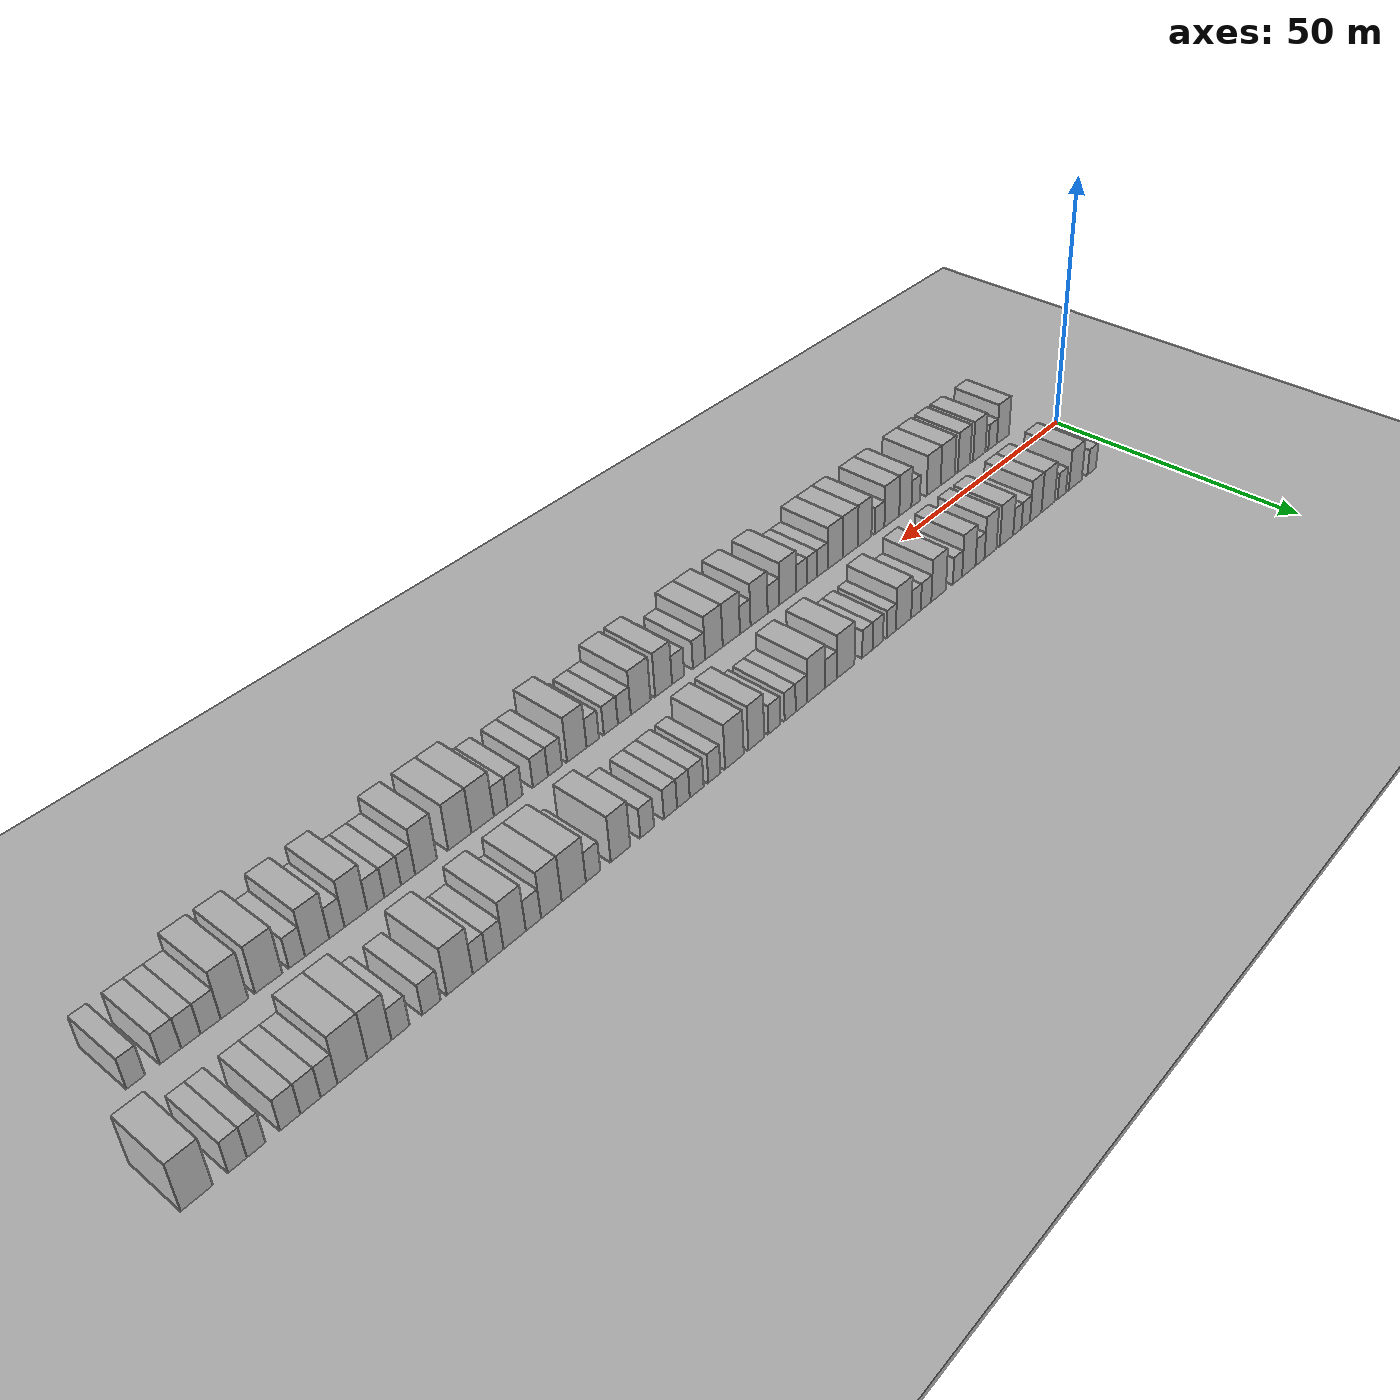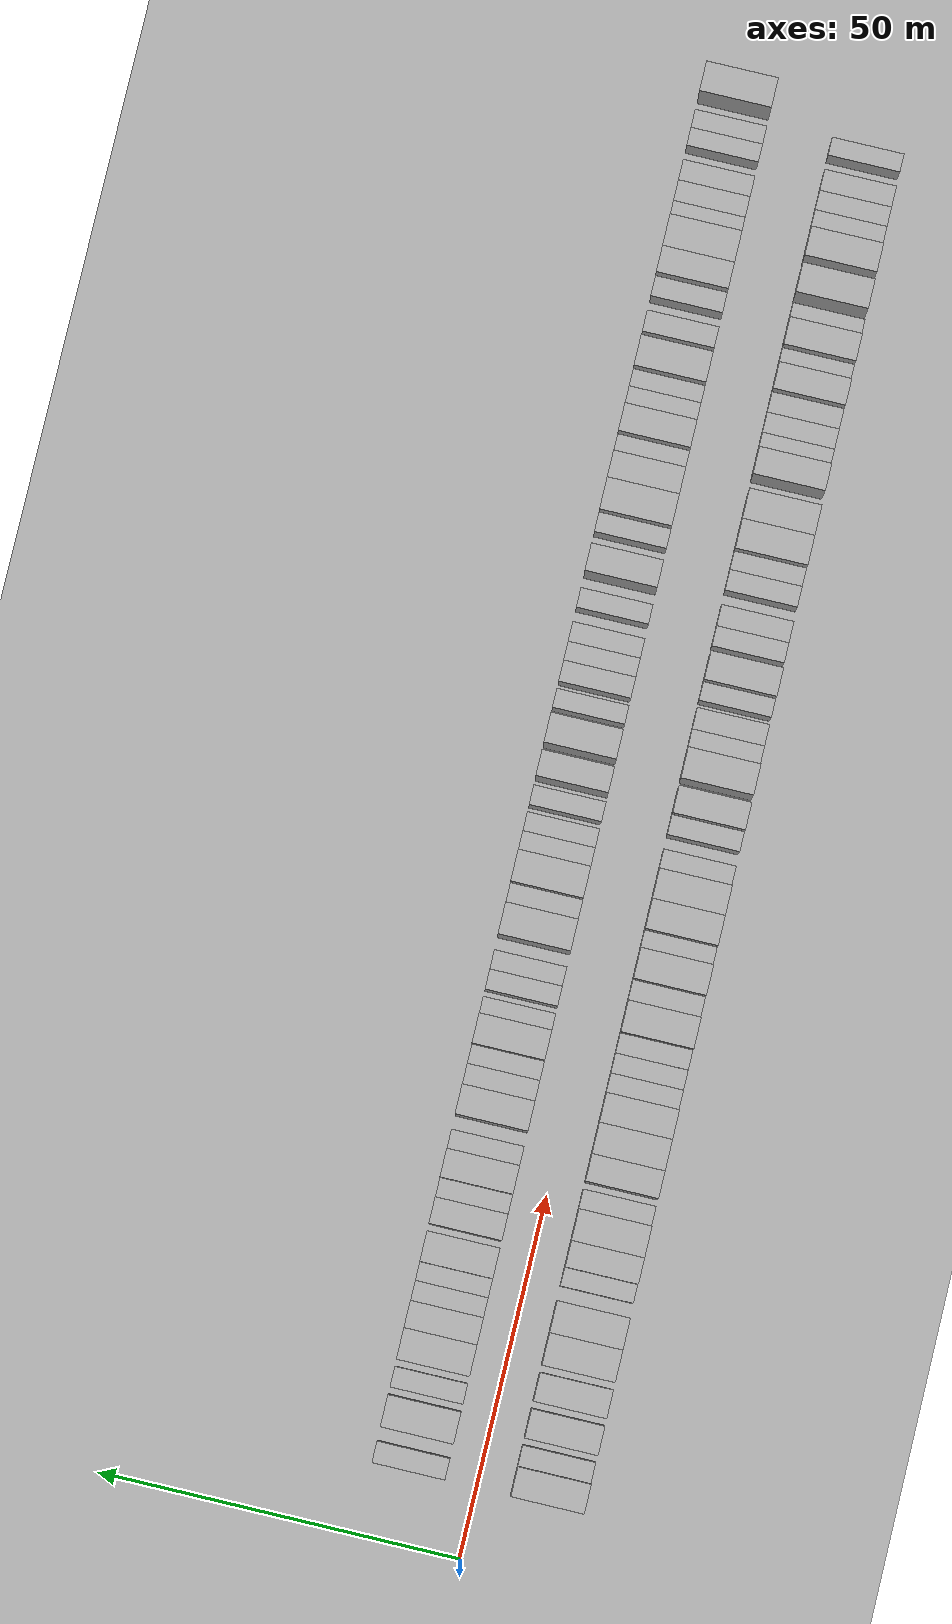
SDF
<?xml version="1.0" encoding="utf-8"?>

<sdf version="1.6">

   <world name="default">

      <gui fullscreen="0">

         <camera name="user_camera">

            <pose>-15 0 4.57585 0 0 0</pose>

            <view_controller>orbit</view_controller>

         </camera>

      </gui>

      <scene>

         <sky>

           <clouds>

             <speed>12</speed>

           </clouds>

         </sky>

         <ambient>0.4 0.4 0.4 1</ambient>

         <background>0.7 0.7 0.7 1</background>

         <shadows>1</shadows>

      </scene>

      <gravity>0 0 -9.8066</gravity>

      <magnetic_field>6e-06 2.3e-05 -4.2e-05</magnetic_field>

      <physics default="0" name="default_physics" type="ode">

         <ode>

            <solver>

               <type>quick</type>

               <iters>10</iters>

               <sor>1.0</sor>

               <use_dynamic_moi_rescaling>0</use_dynamic_moi_rescaling>

            </solver>

            <constraints>

               <cfm>0</cfm>

               <erp>0.2</erp>

               <contact_max_correcting_vel>100</contact_max_correcting_vel>

               <contact_surface_layer>0.001</contact_surface_layer>

            </constraints>

         </ode>

         <max_step_size>0.004</max_step_size>

         <real_time_factor>1</real_time_factor>

         <real_time_update_rate>250</real_time_update_rate>

      </physics>

      <light name="sun" type="directional">

         <cast_shadows>1</cast_shadows>

         <pose>0 0 10 0 0 0</pose>

         <diffuse>0.8 0.8 0.8 1</diffuse>

         <specular>0.2 0.2 0.2 1</specular>

         <attenuation>

            <range>1000</range>

            <constant>0.9</constant>

            <linear>0.01</linear>

            <quadratic>0.001</quadratic>

         </attenuation>

         <direction>-0.5 0.1 -0.9</direction>

      </light>

      <include>

         <name>ground_plane_1</name>

         <uri>model://HANNAS_ground_plane</uri>

         <pose>0 0 0  0 0 0</pose>

      </include>

      <include>

         <name>ground_plane_2</name>

         <uri>model://HANNAS_ground_plane</uri>

         <pose>100 0 0  0 0 0</pose>

      </include>

      <model name="building_1">

         <static>1</static>

         <pose frame="">11.4663 9.5000 0 0.000000 0.000000 1.570796</pose>

         <link name="link">

            <pose frame="">0 0 3.00 0 0 0</pose>

            <collision name="collision">

               <geometry>

                  <box>

                     <size>10.0000 2.9326 6.0000</size>

                  </box>

               </geometry>

               <max_contacts>10</max_contacts>

               <surface>

                  <contact>

                     <ode/>

                  </contact>

                  <bounce/>

                  <friction>

                     <torsional>

                        <ode/>

                     </torsional>

                     <ode/>

                  </friction>

               </surface>

            </collision>

            <visual name="visual">

               <cast_shadows>0</cast_shadows>

               <geometry>

                  <box>

                     <size>10.0000 2.9326 6.0000</size>

                  </box>

               </geometry>

               <material>

                  <script>

                     <uri>model://HANNAS_wall/materials/scripts</uri>

                     <uri>model://HANNAS_wall/materials/textures</uri>

                     <name>vrc/HANNAS_wall</name>

                  </script>

               </material>

            </visual>

            <self_collide>0</self_collide>

            <enable_wind>0</enable_wind>

            <kinematic>0</kinematic>

         </link>

      </model>

      <model name="building_2">

         <static>1</static>

         <pose frame="">17.1195 9.5000 0 0.000000 0.000000 1.570796</pose>

         <link name="link">

            <pose frame="">0 0 4.50 0 0 0</pose>

            <collision name="collision">

               <geometry>

                  <box>

                     <size>10.0000 4.3737 9.0000</size>

                  </box>

               </geometry>

               <max_contacts>10</max_contacts>

               <surface>

                  <contact>

                     <ode/>

                  </contact>

                  <bounce/>

                  <friction>

                     <torsional>

                        <ode/>

                     </torsional>

                     <ode/>

                  </friction>

               </surface>

            </collision>

            <visual name="visual">

               <cast_shadows>0</cast_shadows>

               <geometry>

                  <box>

                     <size>10.0000 4.3737 9.0000</size>

                  </box>

               </geometry>

               <material>

                  <script>

                     <uri>model://HANNAS_wall/materials/scripts</uri>

                     <uri>model://HANNAS_wall/materials/textures</uri>

                     <name>vrc/HANNAS_wall</name>

                  </script>

               </material>

            </visual>

            <self_collide>0</self_collide>

            <enable_wind>0</enable_wind>

            <kinematic>0</kinematic>

         </link>

      </model>

      <model name="building_3">

         <static>1</static>

         <pose frame="">21.7086 9.5000 0 0.000000 0.000000 1.570796</pose>

         <link name="link">

            <pose frame="">0 0 3.00 0 0 0</pose>

            <collision name="collision">

               <geometry>

                  <box>

                     <size>10.0000 2.8046 6.0000</size>

                  </box>

               </geometry>

               <max_contacts>10</max_contacts>

               <surface>

                  <contact>

                     <ode/>

                  </contact>

                  <bounce/>

                  <friction>

                     <torsional>

                        <ode/>

                     </torsional>

                     <ode/>

                  </friction>

               </surface>

            </collision>

            <visual name="visual">

               <cast_shadows>0</cast_shadows>

               <geometry>

                  <box>

                     <size>10.0000 2.8046 6.0000</size>

                  </box>

               </geometry>

               <material>

                  <script>

                     <uri>model://HANNAS_wall/materials/scripts</uri>

                     <uri>model://HANNAS_wall/materials/textures</uri>

                     <name>vrc/HANNAS_wall</name>

                  </script>

               </material>

            </visual>

            <self_collide>0</self_collide>

            <enable_wind>0</enable_wind>

            <kinematic>0</kinematic>

         </link>

      </model>

      <model name="building_4">

         <static>1</static>

         <pose frame="">26.2625 9.5000 0 0.000000 0.000000 1.570796</pose>

         <link name="link">

            <pose frame="">0 0 4.50 0 0 0</pose>

            <collision name="collision">

               <geometry>

                  <box>

                     <size>10.0000 4.3031 9.0000</size>

                  </box>

               </geometry>

               <max_contacts>10</max_contacts>

               <surface>

                  <contact>

                     <ode/>

                  </contact>

                  <bounce/>

                  <friction>

                     <torsional>

                        <ode/>

                     </torsional>

                     <ode/>

                  </friction>

               </surface>

            </collision>

            <visual name="visual">

               <cast_shadows>0</cast_shadows>

               <geometry>

                  <box>

                     <size>10.0000 4.3031 9.0000</size>

                  </box>

               </geometry>

               <material>

                  <script>

                     <uri>model://HANNAS_wall/materials/scripts</uri>

                     <uri>model://HANNAS_wall/materials/textures</uri>

                     <name>vrc/HANNAS_wall</name>

                  </script>

               </material>

            </visual>

            <self_collide>0</self_collide>

            <enable_wind>0</enable_wind>

            <kinematic>0</kinematic>

         </link>

      </model>

      <model name="building_5">

         <static>1</static>

         <pose frame="">30.2698 9.5000 0 0.000000 0.000000 1.570796</pose>

         <link name="link">

            <pose frame="">0 0 4.50 0 0 0</pose>

            <collision name="collision">

               <geometry>

                  <box>

                     <size>10.0000 3.7114 9.0000</size>

                  </box>

               </geometry>

               <max_contacts>10</max_contacts>

               <surface>

                  <contact>

                     <ode/>

                  </contact>

                  <bounce/>

                  <friction>

                     <torsional>

                        <ode/>

                     </torsional>

                     <ode/>

                  </friction>

               </surface>

            </collision>

            <visual name="visual">

               <cast_shadows>0</cast_shadows>

               <geometry>

                  <box>

                     <size>10.0000 3.7114 9.0000</size>

                  </box>

               </geometry>

               <material>

                  <script>

                     <uri>model://HANNAS_wall/materials/scripts</uri>

                     <uri>model://HANNAS_wall/materials/textures</uri>

                     <name>vrc/HANNAS_wall</name>

                  </script>

               </material>

            </visual>

            <self_collide>0</self_collide>

            <enable_wind>0</enable_wind>

            <kinematic>0</kinematic>

         </link>

      </model>

      <model name="building_6">

         <static>1</static>

         <pose frame="">33.4871 9.5000 0 0.000000 0.000000 1.570796</pose>

         <link name="link">

            <pose frame="">0 0 3.00 0 0 0</pose>

            <collision name="collision">

               <geometry>

                  <box>

                     <size>10.0000 2.7232 6.0000</size>

                  </box>

               </geometry>

               <max_contacts>10</max_contacts>

               <surface>

                  <contact>

                     <ode/>

                  </contact>

                  <bounce/>

                  <friction>

                     <torsional>

                        <ode/>

                     </torsional>

                     <ode/>

                  </friction>

               </surface>

            </collision>

            <visual name="visual">

               <cast_shadows>0</cast_shadows>

               <geometry>

                  <box>

                     <size>10.0000 2.7232 6.0000</size>

                  </box>

               </geometry>

               <material>

                  <script>

                     <uri>model://HANNAS_wall/materials/scripts</uri>

                     <uri>model://HANNAS_wall/materials/textures</uri>

                     <name>vrc/HANNAS_wall</name>

                  </script>

               </material>

            </visual>

            <self_collide>0</self_collide>

            <enable_wind>0</enable_wind>

            <kinematic>0</kinematic>

         </link>

      </model>

      <model name="building_7">

         <static>1</static>

         <pose frame="">36.1330 9.5000 0 0.000000 0.000000 1.570796</pose>

         <link name="link">

            <pose frame="">0 0 3.00 0 0 0</pose>

            <collision name="collision">

               <geometry>

                  <box>

                     <size>10.0000 2.5685 6.0000</size>

                  </box>

               </geometry>

               <max_contacts>10</max_contacts>

               <surface>

                  <contact>

                     <ode/>

                  </contact>

                  <bounce/>

                  <friction>

                     <torsional>

                        <ode/>

                     </torsional>

                     <ode/>

                  </friction>

               </surface>

            </collision>

            <visual name="visual">

               <cast_shadows>0</cast_shadows>

               <geometry>

                  <box>

                     <size>10.0000 2.5685 6.0000</size>

                  </box>

               </geometry>

               <material>

                  <script>

                     <uri>model://HANNAS_wall/materials/scripts</uri>

                     <uri>model://HANNAS_wall/materials/textures</uri>

                     <name>vrc/HANNAS_wall</name>

                  </script>

               </material>

            </visual>

            <self_collide>0</self_collide>

            <enable_wind>0</enable_wind>

            <kinematic>0</kinematic>

         </link>

      </model>

      <model name="building_8">

         <static>1</static>

         <pose frame="">39.5141 9.5000 0 0.000000 0.000000 1.570796</pose>

         <link name="link">

            <pose frame="">0 0 4.50 0 0 0</pose>

            <collision name="collision">

               <geometry>

                  <box>

                     <size>10.0000 4.1938 9.0000</size>

                  </box>

               </geometry>

               <max_contacts>10</max_contacts>

               <surface>

                  <contact>

                     <ode/>

                  </contact>

                  <bounce/>

                  <friction>

                     <torsional>

                        <ode/>

                     </torsional>

                     <ode/>

                  </friction>

               </surface>

            </collision>

            <visual name="visual">

               <cast_shadows>0</cast_shadows>

               <geometry>

                  <box>

                     <size>10.0000 4.1938 9.0000</size>

                  </box>

               </geometry>

               <material>

                  <script>

                     <uri>model://HANNAS_wall/materials/scripts</uri>

                     <uri>model://HANNAS_wall/materials/textures</uri>

                     <name>vrc/HANNAS_wall</name>

                  </script>

               </material>

            </visual>

            <self_collide>0</self_collide>

            <enable_wind>0</enable_wind>

            <kinematic>0</kinematic>

         </link>

      </model>

      <model name="building_9">

         <static>1</static>

         <pose frame="">44.4281 9.5000 0 0.000000 0.000000 1.570796</pose>

         <link name="link">

            <pose frame="">0 0 4.50 0 0 0</pose>

            <collision name="collision">

               <geometry>

                  <box>

                     <size>10.0000 3.6342 9.0000</size>

                  </box>

               </geometry>

               <max_contacts>10</max_contacts>

               <surface>

                  <contact>

                     <ode/>

                  </contact>

                  <bounce/>

                  <friction>

                     <torsional>

                        <ode/>

                     </torsional>

                     <ode/>

                  </friction>

               </surface>

            </collision>

            <visual name="visual">

               <cast_shadows>0</cast_shadows>

               <geometry>

                  <box>

                     <size>10.0000 3.6342 9.0000</size>

                  </box>

               </geometry>

               <material>

                  <script>

                     <uri>model://HANNAS_wall/materials/scripts</uri>

                     <uri>model://HANNAS_wall/materials/textures</uri>

                     <name>vrc/HANNAS_wall</name>

                  </script>

               </material>

            </visual>

            <self_collide>0</self_collide>

            <enable_wind>0</enable_wind>

            <kinematic>0</kinematic>

         </link>

      </model>

      <model name="building_10">

         <static>1</static>

         <pose frame="">47.5984 9.5000 0 0.000000 0.000000 1.570796</pose>

         <link name="link">

            <pose frame="">0 0 3.00 0 0 0</pose>

            <collision name="collision">

               <geometry>

                  <box>

                     <size>10.0000 2.7064 6.0000</size>

                  </box>

               </geometry>

               <max_contacts>10</max_contacts>

               <surface>

                  <contact>

                     <ode/>

                  </contact>

                  <bounce/>

                  <friction>

                     <torsional>

                        <ode/>

                     </torsional>

                     <ode/>

                  </friction>

               </surface>

            </collision>

            <visual name="visual">

               <cast_shadows>0</cast_shadows>

               <geometry>

                  <box>

                     <size>10.0000 2.7064 6.0000</size>

                  </box>

               </geometry>

               <material>

                  <script>

                     <uri>model://HANNAS_wall/materials/scripts</uri>

                     <uri>model://HANNAS_wall/materials/textures</uri>

                     <name>vrc/HANNAS_wall</name>

                  </script>

               </material>

            </visual>

            <self_collide>0</self_collide>

            <enable_wind>0</enable_wind>

            <kinematic>0</kinematic>

         </link>

      </model>

      <model name="building_11">

         <static>1</static>

         <pose frame="">50.9195 9.5000 0 0.000000 0.000000 1.570796</pose>

         <link name="link">

            <pose frame="">0 0 4.50 0 0 0</pose>

            <collision name="collision">

               <geometry>

                  <box>

                     <size>10.0000 3.9358 9.0000</size>

                  </box>

               </geometry>

               <max_contacts>10</max_contacts>

               <surface>

                  <contact>

                     <ode/>

                  </contact>

                  <bounce/>

                  <friction>

                     <torsional>

                        <ode/>

                     </torsional>

                     <ode/>

                  </friction>

               </surface>

            </collision>

            <visual name="visual">

               <cast_shadows>0</cast_shadows>

               <geometry>

                  <box>

                     <size>10.0000 3.9358 9.0000</size>

                  </box>

               </geometry>

               <material>

                  <script>

                     <uri>model://HANNAS_wall/materials/scripts</uri>

                     <uri>model://HANNAS_wall/materials/textures</uri>

                     <name>vrc/HANNAS_wall</name>

                  </script>

               </material>

            </visual>

            <self_collide>0</self_collide>

            <enable_wind>0</enable_wind>

            <kinematic>0</kinematic>

         </link>

      </model>

      <model name="building_12">

         <static>1</static>

         <pose frame="">54.2361 9.5000 0 0.000000 0.000000 1.570796</pose>

         <link name="link">

            <pose frame="">0 0 3.00 0 0 0</pose>

            <collision name="collision">

               <geometry>

                  <box>

                     <size>10.0000 2.6974 6.0000</size>

                  </box>

               </geometry>

               <max_contacts>10</max_contacts>

               <surface>

                  <contact>

                     <ode/>

                  </contact>

                  <bounce/>

                  <friction>

                     <torsional>

                        <ode/>

                     </torsional>

                     <ode/>

                  </friction>

               </surface>

            </collision>

            <visual name="visual">

               <cast_shadows>0</cast_shadows>

               <geometry>

                  <box>

                     <size>10.0000 2.6974 6.0000</size>

                  </box>

               </geometry>

               <material>

                  <script>

                     <uri>model://HANNAS_wall/materials/scripts</uri>

                     <uri>model://HANNAS_wall/materials/textures</uri>

                     <name>vrc/HANNAS_wall</name>

                  </script>

               </material>

            </visual>

            <self_collide>0</self_collide>

            <enable_wind>0</enable_wind>

            <kinematic>0</kinematic>

         </link>

      </model>

      <model name="building_13">

         <static>1</static>

         <pose frame="">59.6473 9.5000 0 0.000000 0.000000 1.570796</pose>

         <link name="link">

            <pose frame="">0 0 4.50 0 0 0</pose>

            <collision name="collision">

               <geometry>

                  <box>

                     <size>10.0000 4.1249 9.0000</size>

                  </box>

               </geometry>

               <max_contacts>10</max_contacts>

               <surface>

                  <contact>

                     <ode/>

                  </contact>

                  <bounce/>

                  <friction>

                     <torsional>

                        <ode/>

                     </torsional>

                     <ode/>

                  </friction>

               </surface>

            </collision>

            <visual name="visual">

               <cast_shadows>0</cast_shadows>

               <geometry>

                  <box>

                     <size>10.0000 4.1249 9.0000</size>

                  </box>

               </geometry>

               <material>

                  <script>

                     <uri>model://HANNAS_wall/materials/scripts</uri>

                     <uri>model://HANNAS_wall/materials/textures</uri>

                     <name>vrc/HANNAS_wall</name>

                  </script>

               </material>

            </visual>

            <self_collide>0</self_collide>

            <enable_wind>0</enable_wind>

            <kinematic>0</kinematic>

         </link>

      </model>

      <model name="building_14">

         <static>1</static>

         <pose frame="">63.1792 9.5000 0 0.000000 0.000000 1.570796</pose>

         <link name="link">

            <pose frame="">0 0 3.00 0 0 0</pose>

            <collision name="collision">

               <geometry>

                  <box>

                     <size>10.0000 2.9390 6.0000</size>

                  </box>

               </geometry>

               <max_contacts>10</max_contacts>

               <surface>

                  <contact>

                     <ode/>

                  </contact>

                  <bounce/>

                  <friction>

                     <torsional>

                        <ode/>

                     </torsional>

                     <ode/>

                  </friction>

               </surface>

            </collision>

            <visual name="visual">

               <cast_shadows>0</cast_shadows>

               <geometry>

                  <box>

                     <size>10.0000 2.9390 6.0000</size>

                  </box>

               </geometry>

               <material>

                  <script>

                     <uri>model://HANNAS_wall/materials/scripts</uri>

                     <uri>model://HANNAS_wall/materials/textures</uri>

                     <name>vrc/HANNAS_wall</name>

                  </script>

               </material>

            </visual>

            <self_collide>0</self_collide>

            <enable_wind>0</enable_wind>

            <kinematic>0</kinematic>

         </link>

      </model>

      <model name="building_15">

         <static>1</static>

         <pose frame="">65.9733 9.5000 0 0.000000 0.000000 1.570796</pose>

         <link name="link">

            <pose frame="">0 0 3.00 0 0 0</pose>

            <collision name="collision">

               <geometry>

                  <box>

                     <size>10.0000 2.6491 6.0000</size>

                  </box>

               </geometry>

               <max_contacts>10</max_contacts>

               <surface>

                  <contact>

                     <ode/>

                  </contact>

                  <bounce/>

                  <friction>

                     <torsional>

                        <ode/>

                     </torsional>

                     <ode/>

                  </friction>

               </surface>

            </collision>

            <visual name="visual">

               <cast_shadows>0</cast_shadows>

               <geometry>

                  <box>

                     <size>10.0000 2.6491 6.0000</size>

                  </box>

               </geometry>

               <material>

                  <script>

                     <uri>model://HANNAS_wall/materials/scripts</uri>

                     <uri>model://HANNAS_wall/materials/textures</uri>

                     <name>vrc/HANNAS_wall</name>

                  </script>

               </material>

            </visual>

            <self_collide>0</self_collide>

            <enable_wind>0</enable_wind>

            <kinematic>0</kinematic>

         </link>

      </model>

      <model name="building_16">

         <static>1</static>

         <pose frame="">69.3737 9.5000 0 0.000000 0.000000 1.570796</pose>

         <link name="link">

            <pose frame="">0 0 4.50 0 0 0</pose>

            <collision name="collision">

               <geometry>

                  <box>

                     <size>10.0000 4.1518 9.0000</size>

                  </box>

               </geometry>

               <max_contacts>10</max_contacts>

               <surface>

                  <contact>

                     <ode/>

                  </contact>

                  <bounce/>

                  <friction>

                     <torsional>

                        <ode/>

                     </torsional>

                     <ode/>

                  </friction>

               </surface>

            </collision>

            <visual name="visual">

               <cast_shadows>0</cast_shadows>

               <geometry>

                  <box>

                     <size>10.0000 4.1518 9.0000</size>

                  </box>

               </geometry>

               <material>

                  <script>

                     <uri>model://HANNAS_wall/materials/scripts</uri>

                     <uri>model://HANNAS_wall/materials/textures</uri>

                     <name>vrc/HANNAS_wall</name>

                  </script>

               </material>

            </visual>

            <self_collide>0</self_collide>

            <enable_wind>0</enable_wind>

            <kinematic>0</kinematic>

         </link>

      </model>

      <model name="building_17">

         <static>1</static>

         <pose frame="">72.6612 9.5000 0 0.000000 0.000000 1.570796</pose>

         <link name="link">

            <pose frame="">0 0 3.00 0 0 0</pose>

            <collision name="collision">

               <geometry>

                  <box>

                     <size>10.0000 2.4232 6.0000</size>

                  </box>

               </geometry>

               <max_contacts>10</max_contacts>

               <surface>

                  <contact>

                     <ode/>

                  </contact>

                  <bounce/>

                  <friction>

                     <torsional>

                        <ode/>

                     </torsional>

                     <ode/>

                  </friction>

               </surface>

            </collision>

            <visual name="visual">

               <cast_shadows>0</cast_shadows>

               <geometry>

                  <box>

                     <size>10.0000 2.4232 6.0000</size>

                  </box>

               </geometry>

               <material>

                  <script>

                     <uri>model://HANNAS_wall/materials/scripts</uri>

                     <uri>model://HANNAS_wall/materials/textures</uri>

                     <name>vrc/HANNAS_wall</name>

                  </script>

               </material>

            </visual>

            <self_collide>0</self_collide>

            <enable_wind>0</enable_wind>

            <kinematic>0</kinematic>

         </link>

      </model>

      <model name="building_18">

         <static>1</static>

         <pose frame="">76.2624 9.5000 0 0.000000 0.000000 1.570796</pose>

         <link name="link">

            <pose frame="">0 0 3.00 0 0 0</pose>

            <collision name="collision">

               <geometry>

                  <box>

                     <size>10.0000 2.7791 6.0000</size>

                  </box>

               </geometry>

               <max_contacts>10</max_contacts>

               <surface>

                  <contact>

                     <ode/>

                  </contact>

                  <bounce/>

                  <friction>

                     <torsional>

                        <ode/>

                     </torsional>

                     <ode/>

                  </friction>

               </surface>

            </collision>

            <visual name="visual">

               <cast_shadows>0</cast_shadows>

               <geometry>

                  <box>

                     <size>10.0000 2.7791 6.0000</size>

                  </box>

               </geometry>

               <material>

                  <script>

                     <uri>model://HANNAS_wall/materials/scripts</uri>

                     <uri>model://HANNAS_wall/materials/textures</uri>

                     <name>vrc/HANNAS_wall</name>

                  </script>

               </material>

            </visual>

            <self_collide>0</self_collide>

            <enable_wind>0</enable_wind>

            <kinematic>0</kinematic>

         </link>

      </model>

      <model name="building_19">

         <static>1</static>

         <pose frame="">78.9810 9.5000 0 0.000000 0.000000 1.570796</pose>

         <link name="link">

            <pose frame="">0 0 3.00 0 0 0</pose>

            <collision name="collision">

               <geometry>

                  <box>

                     <size>10.0000 2.6581 6.0000</size>

                  </box>

               </geometry>

               <max_contacts>10</max_contacts>

               <surface>

                  <contact>

                     <ode/>

                  </contact>

                  <bounce/>

                  <friction>

                     <torsional>

                        <ode/>

                     </torsional>

                     <ode/>

                  </friction>

               </surface>

            </collision>

            <visual name="visual">

               <cast_shadows>0</cast_shadows>

               <geometry>

                  <box>

                     <size>10.0000 2.6581 6.0000</size>

                  </box>

               </geometry>

               <material>

                  <script>

                     <uri>model://HANNAS_wall/materials/scripts</uri>

                     <uri>model://HANNAS_wall/materials/textures</uri>

                     <name>vrc/HANNAS_wall</name>

                  </script>

               </material>

            </visual>

            <self_collide>0</self_collide>

            <enable_wind>0</enable_wind>

            <kinematic>0</kinematic>

         </link>

      </model>

      <model name="building_20">

         <static>1</static>

         <pose frame="">84.5085 9.5000 0 0.000000 0.000000 1.570796</pose>

         <link name="link">

            <pose frame="">0 0 4.50 0 0 0</pose>

            <collision name="collision">

               <geometry>

                  <box>

                     <size>10.0000 4.3968 9.0000</size>

                  </box>

               </geometry>

               <max_contacts>10</max_contacts>

               <surface>

                  <contact>

                     <ode/>

                  </contact>

                  <bounce/>

                  <friction>

                     <torsional>

                        <ode/>

                     </torsional>

                     <ode/>

                  </friction>

               </surface>

            </collision>

            <visual name="visual">

               <cast_shadows>0</cast_shadows>

               <geometry>

                  <box>

                     <size>10.0000 4.3968 9.0000</size>

                  </box>

               </geometry>

               <material>

                  <script>

                     <uri>model://HANNAS_wall/materials/scripts</uri>

                     <uri>model://HANNAS_wall/materials/textures</uri>

                     <name>vrc/HANNAS_wall</name>

                  </script>

               </material>

            </visual>

            <self_collide>0</self_collide>

            <enable_wind>0</enable_wind>

            <kinematic>0</kinematic>

         </link>

      </model>

      <model name="building_21">

         <static>1</static>

         <pose frame="">88.1428 9.5000 0 0.000000 0.000000 1.570796</pose>

         <link name="link">

            <pose frame="">0 0 3.00 0 0 0</pose>

            <collision name="collision">

               <geometry>

                  <box>

                     <size>10.0000 2.8719 6.0000</size>

                  </box>

               </geometry>

               <max_contacts>10</max_contacts>

               <surface>

                  <contact>

                     <ode/>

                  </contact>

                  <bounce/>

                  <friction>

                     <torsional>

                        <ode/>

                     </torsional>

                     <ode/>

                  </friction>

               </surface>

            </collision>

            <visual name="visual">

               <cast_shadows>0</cast_shadows>

               <geometry>

                  <box>

                     <size>10.0000 2.8719 6.0000</size>

                  </box>

               </geometry>

               <material>

                  <script>

                     <uri>model://HANNAS_wall/materials/scripts</uri>

                     <uri>model://HANNAS_wall/materials/textures</uri>

                     <name>vrc/HANNAS_wall</name>

                  </script>

               </material>

            </visual>

            <self_collide>0</self_collide>

            <enable_wind>0</enable_wind>

            <kinematic>0</kinematic>

         </link>

      </model>

      <model name="building_22">

         <static>1</static>

         <pose frame="">91.7803 9.5000 0 0.000000 0.000000 1.570796</pose>

         <link name="link">

            <pose frame="">0 0 4.50 0 0 0</pose>

            <collision name="collision">

               <geometry>

                  <box>

                     <size>10.0000 4.4031 9.0000</size>

                  </box>

               </geometry>

               <max_contacts>10</max_contacts>

               <surface>

                  <contact>

                     <ode/>

                  </contact>

                  <bounce/>

                  <friction>

                     <torsional>

                        <ode/>

                     </torsional>

                     <ode/>

                  </friction>

               </surface>

            </collision>

            <visual name="visual">

               <cast_shadows>0</cast_shadows>

               <geometry>

                  <box>

                     <size>10.0000 4.4031 9.0000</size>

                  </box>

               </geometry>

               <material>

                  <script>

                     <uri>model://HANNAS_wall/materials/scripts</uri>

                     <uri>model://HANNAS_wall/materials/textures</uri>

                     <name>vrc/HANNAS_wall</name>

                  </script>

               </material>

            </visual>

            <self_collide>0</self_collide>

            <enable_wind>0</enable_wind>

            <kinematic>0</kinematic>

         </link>

      </model>

      <model name="building_23">

         <static>1</static>

         <pose frame="">95.3848 9.5000 0 0.000000 0.000000 1.570796</pose>

         <link name="link">

            <pose frame="">0 0 3.00 0 0 0</pose>

            <collision name="collision">

               <geometry>

                  <box>

                     <size>10.0000 2.8060 6.0000</size>

                  </box>

               </geometry>

               <max_contacts>10</max_contacts>

               <surface>

                  <contact>

                     <ode/>

                  </contact>

                  <bounce/>

                  <friction>

                     <torsional>

                        <ode/>

                     </torsional>

                     <ode/>

                  </friction>

               </surface>

            </collision>

            <visual name="visual">

               <cast_shadows>0</cast_shadows>

               <geometry>

                  <box>

                     <size>10.0000 2.8060 6.0000</size>

                  </box>

               </geometry>

               <material>

                  <script>

                     <uri>model://HANNAS_wall/materials/scripts</uri>

                     <uri>model://HANNAS_wall/materials/textures</uri>

                     <name>vrc/HANNAS_wall</name>

                  </script>

               </material>

            </visual>

            <self_collide>0</self_collide>

            <enable_wind>0</enable_wind>

            <kinematic>0</kinematic>

         </link>

      </model>

      <model name="building_24">

         <static>1</static>

         <pose frame="">98.0999 9.5000 0 0.000000 0.000000 1.570796</pose>

         <link name="link">

            <pose frame="">0 0 3.00 0 0 0</pose>

            <collision name="collision">

               <geometry>

                  <box>

                     <size>10.0000 2.6241 6.0000</size>

                  </box>

               </geometry>

               <max_contacts>10</max_contacts>

               <surface>

                  <contact>

                     <ode/>

                  </contact>

                  <bounce/>

                  <friction>

                     <torsional>

                        <ode/>

                     </torsional>

                     <ode/>

                  </friction>

               </surface>

            </collision>

            <visual name="visual">

               <cast_shadows>0</cast_shadows>

               <geometry>

                  <box>

                     <size>10.0000 2.6241 6.0000</size>

                  </box>

               </geometry>

               <material>

                  <script>

                     <uri>model://HANNAS_wall/materials/scripts</uri>

                     <uri>model://HANNAS_wall/materials/textures</uri>

                     <name>vrc/HANNAS_wall</name>

                  </script>

               </material>

            </visual>

            <self_collide>0</self_collide>

            <enable_wind>0</enable_wind>

            <kinematic>0</kinematic>

         </link>

      </model>

      <model name="building_25">

         <static>1</static>

         <pose frame="">101.7796 9.5000 0 0.000000 0.000000 1.570796</pose>

         <link name="link">

            <pose frame="">0 0 3.00 0 0 0</pose>

            <collision name="collision">

               <geometry>

                  <box>

                     <size>10.0000 2.7354 6.0000</size>

                  </box>

               </geometry>

               <max_contacts>10</max_contacts>

               <surface>

                  <contact>

                     <ode/>

                  </contact>

                  <bounce/>

                  <friction>

                     <torsional>

                        <ode/>

                     </torsional>

                     <ode/>

                  </friction>

               </surface>

            </collision>

            <visual name="visual">

               <cast_shadows>0</cast_shadows>

               <geometry>

                  <box>

                     <size>10.0000 2.7354 6.0000</size>

                  </box>

               </geometry>

               <material>

                  <script>

                     <uri>model://HANNAS_wall/materials/scripts</uri>

                     <uri>model://HANNAS_wall/materials/textures</uri>

                     <name>vrc/HANNAS_wall</name>

                  </script>

               </material>

            </visual>

            <self_collide>0</self_collide>

            <enable_wind>0</enable_wind>

            <kinematic>0</kinematic>

         </link>

      </model>

      <model name="building_26">

         <static>1</static>

         <pose frame="">105.9616 9.5000 0 0.000000 0.000000 1.570796</pose>

         <link name="link">

            <pose frame="">0 0 4.50 0 0 0</pose>

            <collision name="collision">

               <geometry>

                  <box>

                     <size>10.0000 3.6286 9.0000</size>

                  </box>

               </geometry>

               <max_contacts>10</max_contacts>

               <surface>

                  <contact>

                     <ode/>

                  </contact>

                  <bounce/>

                  <friction>

                     <torsional>

                        <ode/>

                     </torsional>

                     <ode/>

                  </friction>

               </surface>

            </collision>

            <visual name="visual">

               <cast_shadows>0</cast_shadows>

               <geometry>

                  <box>

                     <size>10.0000 3.6286 9.0000</size>

                  </box>

               </geometry>

               <material>

                  <script>

                     <uri>model://HANNAS_wall/materials/scripts</uri>

                     <uri>model://HANNAS_wall/materials/textures</uri>

                     <name>vrc/HANNAS_wall</name>

                  </script>

               </material>

            </visual>

            <self_collide>0</self_collide>

            <enable_wind>0</enable_wind>

            <kinematic>0</kinematic>

         </link>

      </model>

      <model name="building_27">

         <static>1</static>

         <pose frame="">110.8501 9.5000 0 0.000000 0.000000 1.570796</pose>

         <link name="link">

            <pose frame="">0 0 4.50 0 0 0</pose>

            <collision name="collision">

               <geometry>

                  <box>

                     <size>10.0000 4.1483 9.0000</size>

                  </box>

               </geometry>

               <max_contacts>10</max_contacts>

               <surface>

                  <contact>

                     <ode/>

                  </contact>

                  <bounce/>

                  <friction>

                     <torsional>

                        <ode/>

                     </torsional>

                     <ode/>

                  </friction>

               </surface>

            </collision>

            <visual name="visual">

               <cast_shadows>0</cast_shadows>

               <geometry>

                  <box>

                     <size>10.0000 4.1483 9.0000</size>

                  </box>

               </geometry>

               <material>

                  <script>

                     <uri>model://HANNAS_wall/materials/scripts</uri>

                     <uri>model://HANNAS_wall/materials/textures</uri>

                     <name>vrc/HANNAS_wall</name>

                  </script>

               </material>

            </visual>

            <self_collide>0</self_collide>

            <enable_wind>0</enable_wind>

            <kinematic>0</kinematic>

         </link>

      </model>

      <model name="building_28">

         <static>1</static>

         <pose frame="">115.2413 9.5000 0 0.000000 0.000000 1.570796</pose>

         <link name="link">

            <pose frame="">0 0 3.00 0 0 0</pose>

            <collision name="collision">

               <geometry>

                  <box>

                     <size>10.0000 2.6340 6.0000</size>

                  </box>

               </geometry>

               <max_contacts>10</max_contacts>

               <surface>

                  <contact>

                     <ode/>

                  </contact>

                  <bounce/>

                  <friction>

                     <torsional>

                        <ode/>

                     </torsional>

                     <ode/>

                  </friction>

               </surface>

            </collision>

            <visual name="visual">

               <cast_shadows>0</cast_shadows>

               <geometry>

                  <box>

                     <size>10.0000 2.6340 6.0000</size>

                  </box>

               </geometry>

               <material>

                  <script>

                     <uri>model://HANNAS_wall/materials/scripts</uri>

                     <uri>model://HANNAS_wall/materials/textures</uri>

                     <name>vrc/HANNAS_wall</name>

                  </script>

               </material>

            </visual>

            <self_collide>0</self_collide>

            <enable_wind>0</enable_wind>

            <kinematic>0</kinematic>

         </link>

      </model>

      <model name="building_29">

         <static>1</static>

         <pose frame="">119.0284 9.5000 0 0.000000 0.000000 1.570796</pose>

         <link name="link">

            <pose frame="">0 0 3.00 0 0 0</pose>

            <collision name="collision">

               <geometry>

                  <box>

                     <size>10.0000 2.9403 6.0000</size>

                  </box>

               </geometry>

               <max_contacts>10</max_contacts>

               <surface>

                  <contact>

                     <ode/>

                  </contact>

                  <bounce/>

                  <friction>

                     <torsional>

                        <ode/>

                     </torsional>

                     <ode/>

                  </friction>

               </surface>

            </collision>

            <visual name="visual">

               <cast_shadows>0</cast_shadows>

               <geometry>

                  <box>

                     <size>10.0000 2.9403 6.0000</size>

                  </box>

               </geometry>

               <material>

                  <script>

                     <uri>model://HANNAS_wall/materials/scripts</uri>

                     <uri>model://HANNAS_wall/materials/textures</uri>

                     <name>vrc/HANNAS_wall</name>

                  </script>

               </material>

            </visual>

            <self_collide>0</self_collide>

            <enable_wind>0</enable_wind>

            <kinematic>0</kinematic>

         </link>

      </model>

      <model name="building_30">

         <static>1</static>

         <pose frame="">121.8133 9.5000 0 0.000000 0.000000 1.570796</pose>

         <link name="link">

            <pose frame="">0 0 3.00 0 0 0</pose>

            <collision name="collision">

               <geometry>

                  <box>

                     <size>10.0000 2.6295 6.0000</size>

                  </box>

               </geometry>

               <max_contacts>10</max_contacts>

               <surface>

                  <contact>

                     <ode/>

                  </contact>

                  <bounce/>

                  <friction>

                     <torsional>

                        <ode/>

                     </torsional>

                     <ode/>

                  </friction>

               </surface>

            </collision>

            <visual name="visual">

               <cast_shadows>0</cast_shadows>

               <geometry>

                  <box>

                     <size>10.0000 2.6295 6.0000</size>

                  </box>

               </geometry>

               <material>

                  <script>

                     <uri>model://HANNAS_wall/materials/scripts</uri>

                     <uri>model://HANNAS_wall/materials/textures</uri>

                     <name>vrc/HANNAS_wall</name>

                  </script>

               </material>

            </visual>

            <self_collide>0</self_collide>

            <enable_wind>0</enable_wind>

            <kinematic>0</kinematic>

         </link>

      </model>

      <model name="building_31">

         <static>1</static>

         <pose frame="">124.5011 9.5000 0 0.000000 0.000000 1.570796</pose>

         <link name="link">

            <pose frame="">0 0 3.00 0 0 0</pose>

            <collision name="collision">

               <geometry>

                  <box>

                     <size>10.0000 2.7460 6.0000</size>

                  </box>

               </geometry>

               <max_contacts>10</max_contacts>

               <surface>

                  <contact>

                     <ode/>

                  </contact>

                  <bounce/>

                  <friction>

                     <torsional>

                        <ode/>

                     </torsional>

                     <ode/>

                  </friction>

               </surface>

            </collision>

            <visual name="visual">

               <cast_shadows>0</cast_shadows>

               <geometry>

                  <box>

                     <size>10.0000 2.7460 6.0000</size>

                  </box>

               </geometry>

               <material>

                  <script>

                     <uri>model://HANNAS_wall/materials/scripts</uri>

                     <uri>model://HANNAS_wall/materials/textures</uri>

                     <name>vrc/HANNAS_wall</name>

                  </script>

               </material>

            </visual>

            <self_collide>0</self_collide>

            <enable_wind>0</enable_wind>

            <kinematic>0</kinematic>

         </link>

      </model>

      <model name="building_32">

         <static>1</static>

         <pose frame="">129.2465 9.5000 0 0.000000 0.000000 1.570796</pose>

         <link name="link">

            <pose frame="">0 0 3.00 0 0 0</pose>

            <collision name="collision">

               <geometry>

                  <box>

                     <size>10.0000 2.7448 6.0000</size>

                  </box>

               </geometry>

               <max_contacts>10</max_contacts>

               <surface>

                  <contact>

                     <ode/>

                  </contact>

                  <bounce/>

                  <friction>

                     <torsional>

                        <ode/>

                     </torsional>

                     <ode/>

                  </friction>

               </surface>

            </collision>

            <visual name="visual">

               <cast_shadows>0</cast_shadows>

               <geometry>

                  <box>

                     <size>10.0000 2.7448 6.0000</size>

                  </box>

               </geometry>

               <material>

                  <script>

                     <uri>model://HANNAS_wall/materials/scripts</uri>

                     <uri>model://HANNAS_wall/materials/textures</uri>

                     <name>vrc/HANNAS_wall</name>

                  </script>

               </material>

            </visual>

            <self_collide>0</self_collide>

            <enable_wind>0</enable_wind>

            <kinematic>0</kinematic>

         </link>

      </model>

      <model name="building_33">

         <static>1</static>

         <pose frame="">134.5329 9.5000 0 0.000000 0.000000 1.570796</pose>

         <link name="link">

            <pose frame="">0 0 4.50 0 0 0</pose>

            <collision name="collision">

               <geometry>

                  <box>

                     <size>10.0000 3.8281 9.0000</size>

                  </box>

               </geometry>

               <max_contacts>10</max_contacts>

               <surface>

                  <contact>

                     <ode/>

                  </contact>

                  <bounce/>

                  <friction>

                     <torsional>

                        <ode/>

                     </torsional>

                     <ode/>

                  </friction>

               </surface>

            </collision>

            <visual name="visual">

               <cast_shadows>0</cast_shadows>

               <geometry>

                  <box>

                     <size>10.0000 3.8281 9.0000</size>

                  </box>

               </geometry>

               <material>

                  <script>

                     <uri>model://HANNAS_wall/materials/scripts</uri>

                     <uri>model://HANNAS_wall/materials/textures</uri>

                     <name>vrc/HANNAS_wall</name>

                  </script>

               </material>

            </visual>

            <self_collide>0</self_collide>

            <enable_wind>0</enable_wind>

            <kinematic>0</kinematic>

         </link>

      </model>

      <model name="building_34">

         <static>1</static>

         <pose frame="">139.8159 9.5000 0 0.000000 0.000000 1.570796</pose>

         <link name="link">

            <pose frame="">0 0 3.00 0 0 0</pose>

            <collision name="collision">

               <geometry>

                  <box>

                     <size>10.0000 2.7378 6.0000</size>

                  </box>

               </geometry>

               <max_contacts>10</max_contacts>

               <surface>

                  <contact>

                     <ode/>

                  </contact>

                  <bounce/>

                  <friction>

                     <torsional>

                        <ode/>

                     </torsional>

                     <ode/>

                  </friction>

               </surface>

            </collision>

            <visual name="visual">

               <cast_shadows>0</cast_shadows>

               <geometry>

                  <box>

                     <size>10.0000 2.7378 6.0000</size>

                  </box>

               </geometry>

               <material>

                  <script>

                     <uri>model://HANNAS_wall/materials/scripts</uri>

                     <uri>model://HANNAS_wall/materials/textures</uri>

                     <name>vrc/HANNAS_wall</name>

                  </script>

               </material>

            </visual>

            <self_collide>0</self_collide>

            <enable_wind>0</enable_wind>

            <kinematic>0</kinematic>

         </link>

      </model>

      <model name="building_35">

         <static>1</static>

         <pose frame="">143.4241 9.5000 0 0.000000 0.000000 1.570796</pose>

         <link name="link">

            <pose frame="">0 0 4.50 0 0 0</pose>

            <collision name="collision">

               <geometry>

                  <box>

                     <size>10.0000 4.4787 9.0000</size>

                  </box>

               </geometry>

               <max_contacts>10</max_contacts>

               <surface>

                  <contact>

                     <ode/>

                  </contact>

                  <bounce/>

                  <friction>

                     <torsional>

                        <ode/>

                     </torsional>

                     <ode/>

                  </friction>

               </surface>

            </collision>

            <visual name="visual">

               <cast_shadows>0</cast_shadows>

               <geometry>

                  <box>

                     <size>10.0000 4.4787 9.0000</size>

                  </box>

               </geometry>

               <material>

                  <script>

                     <uri>model://HANNAS_wall/materials/scripts</uri>

                     <uri>model://HANNAS_wall/materials/textures</uri>

                     <name>vrc/HANNAS_wall</name>

                  </script>

               </material>

            </visual>

            <self_collide>0</self_collide>

            <enable_wind>0</enable_wind>

            <kinematic>0</kinematic>

         </link>

      </model>

      <model name="building_36">

         <static>1</static>

         <pose frame="">147.5338 9.5000 0 0.000000 0.000000 1.570796</pose>

         <link name="link">

            <pose frame="">0 0 4.50 0 0 0</pose>

            <collision name="collision">

               <geometry>

                  <box>

                     <size>10.0000 3.7408 9.0000</size>

                  </box>

               </geometry>

               <max_contacts>10</max_contacts>

               <surface>

                  <contact>

                     <ode/>

                  </contact>

                  <bounce/>

                  <friction>

                     <torsional>

                        <ode/>

                     </torsional>

                     <ode/>

                  </friction>

               </surface>

            </collision>

            <visual name="visual">

               <cast_shadows>0</cast_shadows>

               <geometry>

                  <box>

                     <size>10.0000 3.7408 9.0000</size>

                  </box>

               </geometry>

               <material>

                  <script>

                     <uri>model://HANNAS_wall/materials/scripts</uri>

                     <uri>model://HANNAS_wall/materials/textures</uri>

                     <name>vrc/HANNAS_wall</name>

                  </script>

               </material>

            </visual>

            <self_collide>0</self_collide>

            <enable_wind>0</enable_wind>

            <kinematic>0</kinematic>

         </link>

      </model>

      <model name="building_37">

         <static>1</static>

         <pose frame="">150.7700 9.5000 0 0.000000 0.000000 1.570796</pose>

         <link name="link">

            <pose frame="">0 0 3.00 0 0 0</pose>

            <collision name="collision">

               <geometry>

                  <box>

                     <size>10.0000 2.7317 6.0000</size>

                  </box>

               </geometry>

               <max_contacts>10</max_contacts>

               <surface>

                  <contact>

                     <ode/>

                  </contact>

                  <bounce/>

                  <friction>

                     <torsional>

                        <ode/>

                     </torsional>

                     <ode/>

                  </friction>

               </surface>

            </collision>

            <visual name="visual">

               <cast_shadows>0</cast_shadows>

               <geometry>

                  <box>

                     <size>10.0000 2.7317 6.0000</size>

                  </box>

               </geometry>

               <material>

                  <script>

                     <uri>model://HANNAS_wall/materials/scripts</uri>

                     <uri>model://HANNAS_wall/materials/textures</uri>

                     <name>vrc/HANNAS_wall</name>

                  </script>

               </material>

            </visual>

            <self_collide>0</self_collide>

            <enable_wind>0</enable_wind>

            <kinematic>0</kinematic>

         </link>

      </model>

      <model name="building_38">

         <static>1</static>

         <pose frame="">154.0858 9.5000 0 0.000000 0.000000 1.570796</pose>

         <link name="link">

            <pose frame="">0 0 4.50 0 0 0</pose>

            <collision name="collision">

               <geometry>

                  <box>

                     <size>10.0000 3.8998 9.0000</size>

                  </box>

               </geometry>

               <max_contacts>10</max_contacts>

               <surface>

                  <contact>

                     <ode/>

                  </contact>

                  <bounce/>

                  <friction>

                     <torsional>

                        <ode/>

                     </torsional>

                     <ode/>

                  </friction>

               </surface>

            </collision>

            <visual name="visual">

               <cast_shadows>0</cast_shadows>

               <geometry>

                  <box>

                     <size>10.0000 3.8998 9.0000</size>

                  </box>

               </geometry>

               <material>

                  <script>

                     <uri>model://HANNAS_wall/materials/scripts</uri>

                     <uri>model://HANNAS_wall/materials/textures</uri>

                     <name>vrc/HANNAS_wall</name>

                  </script>

               </material>

            </visual>

            <self_collide>0</self_collide>

            <enable_wind>0</enable_wind>

            <kinematic>0</kinematic>

         </link>

      </model>

      <model name="building_39">

         <static>1</static>

         <pose frame="">157.4533 9.5000 0 0.000000 0.000000 1.570796</pose>

         <link name="link">

            <pose frame="">0 0 3.00 0 0 0</pose>

            <collision name="collision">

               <geometry>

                  <box>

                     <size>10.0000 2.8353 6.0000</size>

                  </box>

               </geometry>

               <max_contacts>10</max_contacts>

               <surface>

                  <contact>

                     <ode/>

                  </contact>

                  <bounce/>

                  <friction>

                     <torsional>

                        <ode/>

                     </torsional>

                     <ode/>

                  </friction>

               </surface>

            </collision>

            <visual name="visual">

               <cast_shadows>0</cast_shadows>

               <geometry>

                  <box>

                     <size>10.0000 2.8353 6.0000</size>

                  </box>

               </geometry>

               <material>

                  <script>

                     <uri>model://HANNAS_wall/materials/scripts</uri>

                     <uri>model://HANNAS_wall/materials/textures</uri>

                     <name>vrc/HANNAS_wall</name>

                  </script>

               </material>

            </visual>

            <self_collide>0</self_collide>

            <enable_wind>0</enable_wind>

            <kinematic>0</kinematic>

         </link>

      </model>

      <model name="building_40">

         <static>1</static>

         <pose frame="">160.0796 9.5000 0 0.000000 0.000000 1.570796</pose>

         <link name="link">

            <pose frame="">0 0 3.00 0 0 0</pose>

            <collision name="collision">

               <geometry>

                  <box>

                     <size>10.0000 2.4172 6.0000</size>

                  </box>

               </geometry>

               <max_contacts>10</max_contacts>

               <surface>

                  <contact>

                     <ode/>

                  </contact>

                  <bounce/>

                  <friction>

                     <torsional>

                        <ode/>

                     </torsional>

                     <ode/>

                  </friction>

               </surface>

            </collision>

            <visual name="visual">

               <cast_shadows>0</cast_shadows>

               <geometry>

                  <box>

                     <size>10.0000 2.4172 6.0000</size>

                  </box>

               </geometry>

               <material>

                  <script>

                     <uri>model://HANNAS_wall/materials/scripts</uri>

                     <uri>model://HANNAS_wall/materials/textures</uri>

                     <name>vrc/HANNAS_wall</name>

                  </script>

               </material>

            </visual>

            <self_collide>0</self_collide>

            <enable_wind>0</enable_wind>

            <kinematic>0</kinematic>

         </link>

      </model>

      <model name="building_41">

         <static>1</static>

         <pose frame="">163.4362 9.5000 0 0.000000 0.000000 1.570796</pose>

         <link name="link">

            <pose frame="">0 0 4.50 0 0 0</pose>

            <collision name="collision">

               <geometry>

                  <box>

                     <size>10.0000 4.2960 9.0000</size>

                  </box>

               </geometry>

               <max_contacts>10</max_contacts>

               <surface>

                  <contact>

                     <ode/>

                  </contact>

                  <bounce/>

                  <friction>

                     <torsional>

                        <ode/>

                     </torsional>

                     <ode/>

                  </friction>

               </surface>

            </collision>

            <visual name="visual">

               <cast_shadows>0</cast_shadows>

               <geometry>

                  <box>

                     <size>10.0000 4.2960 9.0000</size>

                  </box>

               </geometry>

               <material>

                  <script>

                     <uri>model://HANNAS_wall/materials/scripts</uri>

                     <uri>model://HANNAS_wall/materials/textures</uri>

                     <name>vrc/HANNAS_wall</name>

                  </script>

               </material>

            </visual>

            <self_collide>0</self_collide>

            <enable_wind>0</enable_wind>

            <kinematic>0</kinematic>

         </link>

      </model>

      <model name="building_42">

         <static>1</static>

         <pose frame="">168.0691 9.5000 0 0.000000 0.000000 1.570796</pose>

         <link name="link">

            <pose frame="">0 0 3.00 0 0 0</pose>

            <collision name="collision">

               <geometry>

                  <box>

                     <size>10.0000 2.9698 6.0000</size>

                  </box>

               </geometry>

               <max_contacts>10</max_contacts>

               <surface>

                  <contact>

                     <ode/>

                  </contact>

                  <bounce/>

                  <friction>

                     <torsional>

                        <ode/>

                     </torsional>

                     <ode/>

                  </friction>

               </surface>

            </collision>

            <visual name="visual">

               <cast_shadows>0</cast_shadows>

               <geometry>

                  <box>

                     <size>10.0000 2.9698 6.0000</size>

                  </box>

               </geometry>

               <material>

                  <script>

                     <uri>model://HANNAS_wall/materials/scripts</uri>

                     <uri>model://HANNAS_wall/materials/textures</uri>

                     <name>vrc/HANNAS_wall</name>

                  </script>

               </material>

            </visual>

            <self_collide>0</self_collide>

            <enable_wind>0</enable_wind>

            <kinematic>0</kinematic>

         </link>

      </model>

      <model name="building_43">

         <static>1</static>

         <pose frame="">172.9740 9.5000 0 0.000000 0.000000 1.570796</pose>

         <link name="link">

            <pose frame="">0 0 3.00 0 0 0</pose>

            <collision name="collision">

               <geometry>

                  <box>

                     <size>10.0000 2.8401 6.0000</size>

                  </box>

               </geometry>

               <max_contacts>10</max_contacts>

               <surface>

                  <contact>

                     <ode/>

                  </contact>

                  <bounce/>

                  <friction>

                     <torsional>

                        <ode/>

                     </torsional>

                     <ode/>

                  </friction>

               </surface>

            </collision>

            <visual name="visual">

               <cast_shadows>0</cast_shadows>

               <geometry>

                  <box>

                     <size>10.0000 2.8401 6.0000</size>

                  </box>

               </geometry>

               <material>

                  <script>

                     <uri>model://HANNAS_wall/materials/scripts</uri>

                     <uri>model://HANNAS_wall/materials/textures</uri>

                     <name>vrc/HANNAS_wall</name>

                  </script>

               </material>

            </visual>

            <self_collide>0</self_collide>

            <enable_wind>0</enable_wind>

            <kinematic>0</kinematic>

         </link>

      </model>

      <model name="building_44">

         <static>1</static>

         <pose frame="">176.2465 9.5000 0 0.000000 0.000000 1.570796</pose>

         <link name="link">

            <pose frame="">0 0 4.50 0 0 0</pose>

            <collision name="collision">

               <geometry>

                  <box>

                     <size>10.0000 3.7049 9.0000</size>

                  </box>

               </geometry>

               <max_contacts>10</max_contacts>

               <surface>

                  <contact>

                     <ode/>

                  </contact>

                  <bounce/>

                  <friction>

                     <torsional>

                        <ode/>

                     </torsional>

                     <ode/>

                  </friction>

               </surface>

            </collision>

            <visual name="visual">

               <cast_shadows>0</cast_shadows>

               <geometry>

                  <box>

                     <size>10.0000 3.7049 9.0000</size>

                  </box>

               </geometry>

               <material>

                  <script>

                     <uri>model://HANNAS_wall/materials/scripts</uri>

                     <uri>model://HANNAS_wall/materials/textures</uri>

                     <name>vrc/HANNAS_wall</name>

                  </script>

               </material>

            </visual>

            <self_collide>0</self_collide>

            <enable_wind>0</enable_wind>

            <kinematic>0</kinematic>

         </link>

      </model>

      <model name="building_45">

         <static>1</static>

         <pose frame="">180.3199 9.5000 0 0.000000 0.000000 1.570796</pose>

         <link name="link">

            <pose frame="">0 0 4.50 0 0 0</pose>

            <collision name="collision">

               <geometry>

                  <box>

                     <size>10.0000 4.4417 9.0000</size>

                  </box>

               </geometry>

               <max_contacts>10</max_contacts>

               <surface>

                  <contact>

                     <ode/>

                  </contact>

                  <bounce/>

                  <friction>

                     <torsional>

                        <ode/>

                     </torsional>

                     <ode/>

                  </friction>

               </surface>

            </collision>

            <visual name="visual">

               <cast_shadows>0</cast_shadows>

               <geometry>

                  <box>

                     <size>10.0000 4.4417 9.0000</size>

                  </box>

               </geometry>

               <material>

                  <script>

                     <uri>model://HANNAS_wall/materials/scripts</uri>

                     <uri>model://HANNAS_wall/materials/textures</uri>

                     <name>vrc/HANNAS_wall</name>

                  </script>

               </material>

            </visual>

            <self_collide>0</self_collide>

            <enable_wind>0</enable_wind>

            <kinematic>0</kinematic>

         </link>

      </model>

      <model name="building_46">

         <static>1</static>

         <pose frame="">183.7738 9.5000 0 0.000000 0.000000 1.570796</pose>

         <link name="link">

            <pose frame="">0 0 3.00 0 0 0</pose>

            <collision name="collision">

               <geometry>

                  <box>

                     <size>10.0000 2.4662 6.0000</size>

                  </box>

               </geometry>

               <max_contacts>10</max_contacts>

               <surface>

                  <contact>

                     <ode/>

                  </contact>

                  <bounce/>

                  <friction>

                     <torsional>

                        <ode/>

                     </torsional>

                     <ode/>

                  </friction>

               </surface>

            </collision>

            <visual name="visual">

               <cast_shadows>0</cast_shadows>

               <geometry>

                  <box>

                     <size>10.0000 2.4662 6.0000</size>

                  </box>

               </geometry>

               <material>

                  <script>

                     <uri>model://HANNAS_wall/materials/scripts</uri>

                     <uri>model://HANNAS_wall/materials/textures</uri>

                     <name>vrc/HANNAS_wall</name>

                  </script>

               </material>

            </visual>

            <self_collide>0</self_collide>

            <enable_wind>0</enable_wind>

            <kinematic>0</kinematic>

         </link>

      </model>

      <model name="building_47">

         <static>1</static>

         <pose frame="">186.4688 9.5000 0 0.000000 0.000000 1.570796</pose>

         <link name="link">

            <pose frame="">0 0 3.00 0 0 0</pose>

            <collision name="collision">

               <geometry>

                  <box>

                     <size>10.0000 2.9237 6.0000</size>

                  </box>

               </geometry>

               <max_contacts>10</max_contacts>

               <surface>

                  <contact>

                     <ode/>

                  </contact>

                  <bounce/>

                  <friction>

                     <torsional>

                        <ode/>

                     </torsional>

                     <ode/>

                  </friction>

               </surface>

            </collision>

            <visual name="visual">

               <cast_shadows>0</cast_shadows>

               <geometry>

                  <box>

                     <size>10.0000 2.9237 6.0000</size>

                  </box>

               </geometry>

               <material>

                  <script>

                     <uri>model://HANNAS_wall/materials/scripts</uri>

                     <uri>model://HANNAS_wall/materials/textures</uri>

                     <name>vrc/HANNAS_wall</name>

                  </script>

               </material>

            </visual>

            <self_collide>0</self_collide>

            <enable_wind>0</enable_wind>

            <kinematic>0</kinematic>

         </link>

      </model>

      <model name="building_48">

         <static>1</static>

         <pose frame="">189.3747 9.5000 0 0.000000 0.000000 1.570796</pose>

         <link name="link">

            <pose frame="">0 0 3.00 0 0 0</pose>

            <collision name="collision">

               <geometry>

                  <box>

                     <size>10.0000 2.8881 6.0000</size>

                  </box>

               </geometry>

               <max_contacts>10</max_contacts>

               <surface>

                  <contact>

                     <ode/>

                  </contact>

                  <bounce/>

                  <friction>

                     <torsional>

                        <ode/>

                     </torsional>

                     <ode/>

                  </friction>

               </surface>

            </collision>

            <visual name="visual">

               <cast_shadows>0</cast_shadows>

               <geometry>

                  <box>

                     <size>10.0000 2.8881 6.0000</size>

                  </box>

               </geometry>

               <material>

                  <script>

                     <uri>model://HANNAS_wall/materials/scripts</uri>

                     <uri>model://HANNAS_wall/materials/textures</uri>

                     <name>vrc/HANNAS_wall</name>

                  </script>

               </material>

            </visual>

            <self_collide>0</self_collide>

            <enable_wind>0</enable_wind>

            <kinematic>0</kinematic>

         </link>

      </model>

      <model name="building_49">

         <static>1</static>

         <pose frame="">194.0902 9.5000 0 0.000000 0.000000 1.570796</pose>

         <link name="link">

            <pose frame="">0 0 3.00 0 0 0</pose>

            <collision name="collision">

               <geometry>

                  <box>

                     <size>10.0000 2.5428 6.0000</size>

                  </box>

               </geometry>

               <max_contacts>10</max_contacts>

               <surface>

                  <contact>

                     <ode/>

                  </contact>

                  <bounce/>

                  <friction>

                     <torsional>

                        <ode/>

                     </torsional>

                     <ode/>

                  </friction>

               </surface>

            </collision>

            <visual name="visual">

               <cast_shadows>0</cast_shadows>

               <geometry>

                  <box>

                     <size>10.0000 2.5428 6.0000</size>

                  </box>

               </geometry>

               <material>

                  <script>

                     <uri>model://HANNAS_wall/materials/scripts</uri>

                     <uri>model://HANNAS_wall/materials/textures</uri>

                     <name>vrc/HANNAS_wall</name>

                  </script>

               </material>

            </visual>

            <self_collide>0</self_collide>

            <enable_wind>0</enable_wind>

            <kinematic>0</kinematic>

         </link>

      </model>

      <model name="building_50">

         <static>1</static>

         <pose frame="">196.6348 9.5000 0 0.000000 0.000000 1.570796</pose>

         <link name="link">

            <pose frame="">0 0 3.00 0 0 0</pose>

            <collision name="collision">

               <geometry>

                  <box>

                     <size>10.0000 2.5464 6.0000</size>

                  </box>

               </geometry>

               <max_contacts>10</max_contacts>

               <surface>

                  <contact>

                     <ode/>

                  </contact>

                  <bounce/>

                  <friction>

                     <torsional>

                        <ode/>

                     </torsional>

                     <ode/>

                  </friction>

               </surface>

            </collision>

            <visual name="visual">

               <cast_shadows>0</cast_shadows>

               <geometry>

                  <box>

                     <size>10.0000 2.5464 6.0000</size>

                  </box>

               </geometry>

               <material>

                  <script>

                     <uri>model://HANNAS_wall/materials/scripts</uri>

                     <uri>model://HANNAS_wall/materials/textures</uri>

                     <name>vrc/HANNAS_wall</name>

                  </script>

               </material>

            </visual>

            <self_collide>0</self_collide>

            <enable_wind>0</enable_wind>

            <kinematic>0</kinematic>

         </link>

      </model>

      <model name="building_51">

         <static>1</static>

         <pose frame="">202.0019 9.5000 0 0.000000 0.000000 1.570796</pose>

         <link name="link">

            <pose frame="">0 0 4.50 0 0 0</pose>

            <collision name="collision">

               <geometry>

                  <box>

                     <size>10.0000 4.1879 9.0000</size>

                  </box>

               </geometry>

               <max_contacts>10</max_contacts>

               <surface>

                  <contact>

                     <ode/>

                  </contact>

                  <bounce/>

                  <friction>

                     <torsional>

                        <ode/>

                     </torsional>

                     <ode/>

                  </friction>

               </surface>

            </collision>

            <visual name="visual">

               <cast_shadows>0</cast_shadows>

               <geometry>

                  <box>

                     <size>10.0000 4.1879 9.0000</size>

                  </box>

               </geometry>

               <material>

                  <script>

                     <uri>model://HANNAS_wall/materials/scripts</uri>

                     <uri>model://HANNAS_wall/materials/textures</uri>

                     <name>vrc/HANNAS_wall</name>

                  </script>

               </material>

            </visual>

            <self_collide>0</self_collide>

            <enable_wind>0</enable_wind>

            <kinematic>0</kinematic>

         </link>

      </model>

      <model name="building_52">

         <static>1</static>

         <pose frame="">12.0296 -9.5000 0 0.000000 0.000000 1.570796</pose>

         <link name="link">

            <pose frame="">0 0 4.50 0 0 0</pose>

            <collision name="collision">

               <geometry>

                  <box>

                     <size>10.0000 4.0592 9.0000</size>

                  </box>

               </geometry>

               <max_contacts>10</max_contacts>

               <surface>

                  <contact>

                     <ode/>

                  </contact>

                  <bounce/>

                  <friction>

                     <torsional>

                        <ode/>

                     </torsional>

                     <ode/>

                  </friction>

               </surface>

            </collision>

            <visual name="visual">

               <cast_shadows>0</cast_shadows>

               <geometry>

                  <box>

                     <size>10.0000 4.0592 9.0000</size>

                  </box>

               </geometry>

               <material>

                  <script>

                     <uri>model://HANNAS_wall/materials/scripts</uri>

                     <uri>model://HANNAS_wall/materials/textures</uri>

                     <name>vrc/HANNAS_wall</name>

                  </script>

               </material>

            </visual>

            <self_collide>0</self_collide>

            <enable_wind>0</enable_wind>

            <kinematic>0</kinematic>

         </link>

      </model>

      <model name="building_53">

         <static>1</static>

         <pose frame="">15.4925 -9.5000 0 0.000000 0.000000 1.570796</pose>

         <link name="link">

            <pose frame="">0 0 3.00 0 0 0</pose>

            <collision name="collision">

               <geometry>

                  <box>

                     <size>10.0000 2.8667 6.0000</size>

                  </box>

               </geometry>

               <max_contacts>10</max_contacts>

               <surface>

                  <contact>

                     <ode/>

                  </contact>

                  <bounce/>

                  <friction>

                     <torsional>

                        <ode/>

                     </torsional>

                     <ode/>

                  </friction>

               </surface>

            </collision>

            <visual name="visual">

               <cast_shadows>0</cast_shadows>

               <geometry>

                  <box>

                     <size>10.0000 2.8667 6.0000</size>

                  </box>

               </geometry>

               <material>

                  <script>

                     <uri>model://HANNAS_wall/materials/scripts</uri>

                     <uri>model://HANNAS_wall/materials/textures</uri>

                     <name>vrc/HANNAS_wall</name>

                  </script>

               </material>

            </visual>

            <self_collide>0</self_collide>

            <enable_wind>0</enable_wind>

            <kinematic>0</kinematic>

         </link>

      </model>

      <model name="building_54">

         <static>1</static>

         <pose frame="">19.9274 -9.5000 0 0.000000 0.000000 1.570796</pose>

         <link name="link">

            <pose frame="">0 0 4.50 0 0 0</pose>

            <collision name="collision">

               <geometry>

                  <box>

                     <size>10.0000 4.0031 9.0000</size>

                  </box>

               </geometry>

               <max_contacts>10</max_contacts>

               <surface>

                  <contact>

                     <ode/>

                  </contact>

                  <bounce/>

                  <friction>

                     <torsional>

                        <ode/>

                     </torsional>

                     <ode/>

                  </friction>

               </surface>

            </collision>

            <visual name="visual">

               <cast_shadows>0</cast_shadows>

               <geometry>

                  <box>

                     <size>10.0000 4.0031 9.0000</size>

                  </box>

               </geometry>

               <material>

                  <script>

                     <uri>model://HANNAS_wall/materials/scripts</uri>

                     <uri>model://HANNAS_wall/materials/textures</uri>

                     <name>vrc/HANNAS_wall</name>

                  </script>

               </material>

            </visual>

            <self_collide>0</self_collide>

            <enable_wind>0</enable_wind>

            <kinematic>0</kinematic>

         </link>

      </model>

      <model name="building_55">

         <static>1</static>

         <pose frame="">24.8830 -9.5000 0 0.000000 0.000000 1.570796</pose>

         <link name="link">

            <pose frame="">0 0 4.50 0 0 0</pose>

            <collision name="collision">

               <geometry>

                  <box>

                     <size>10.0000 3.9080 9.0000</size>

                  </box>

               </geometry>

               <max_contacts>10</max_contacts>

               <surface>

                  <contact>

                     <ode/>

                  </contact>

                  <bounce/>

                  <friction>

                     <torsional>

                        <ode/>

                     </torsional>

                     <ode/>

                  </friction>

               </surface>

            </collision>

            <visual name="visual">

               <cast_shadows>0</cast_shadows>

               <geometry>

                  <box>

                     <size>10.0000 3.9080 9.0000</size>

                  </box>

               </geometry>

               <material>

                  <script>

                     <uri>model://HANNAS_wall/materials/scripts</uri>

                     <uri>model://HANNAS_wall/materials/textures</uri>

                     <name>vrc/HANNAS_wall</name>

                  </script>

               </material>

            </visual>

            <self_collide>0</self_collide>

            <enable_wind>0</enable_wind>

            <kinematic>0</kinematic>

         </link>

      </model>

      <model name="building_56">

         <static>1</static>

         <pose frame="">30.0492 -9.5000 0 0.000000 0.000000 1.570796</pose>

         <link name="link">

            <pose frame="">0 0 4.50 0 0 0</pose>

            <collision name="collision">

               <geometry>

                  <box>

                     <size>10.0000 4.4245 9.0000</size>

                  </box>

               </geometry>

               <max_contacts>10</max_contacts>

               <surface>

                  <contact>

                     <ode/>

                  </contact>

                  <bounce/>

                  <friction>

                     <torsional>

                        <ode/>

                     </torsional>

                     <ode/>

                  </friction>

               </surface>

            </collision>

            <visual name="visual">

               <cast_shadows>0</cast_shadows>

               <geometry>

                  <box>

                     <size>10.0000 4.4245 9.0000</size>

                  </box>

               </geometry>

               <material>

                  <script>

                     <uri>model://HANNAS_wall/materials/scripts</uri>

                     <uri>model://HANNAS_wall/materials/textures</uri>

                     <name>vrc/HANNAS_wall</name>

                  </script>

               </material>

            </visual>

            <self_collide>0</self_collide>

            <enable_wind>0</enable_wind>

            <kinematic>0</kinematic>

         </link>

      </model>

      <model name="building_57">

         <static>1</static>

         <pose frame="">34.4392 -9.5000 0 0.000000 0.000000 1.570796</pose>

         <link name="link">

            <pose frame="">0 0 4.50 0 0 0</pose>

            <collision name="collision">

               <geometry>

                  <box>

                     <size>10.0000 4.3555 9.0000</size>

                  </box>

               </geometry>

               <max_contacts>10</max_contacts>

               <surface>

                  <contact>

                     <ode/>

                  </contact>

                  <bounce/>

                  <friction>

                     <torsional>

                        <ode/>

                     </torsional>

                     <ode/>

                  </friction>

               </surface>

            </collision>

            <visual name="visual">

               <cast_shadows>0</cast_shadows>

               <geometry>

                  <box>

                     <size>10.0000 4.3555 9.0000</size>

                  </box>

               </geometry>

               <material>

                  <script>

                     <uri>model://HANNAS_wall/materials/scripts</uri>

                     <uri>model://HANNAS_wall/materials/textures</uri>

                     <name>vrc/HANNAS_wall</name>

                  </script>

               </material>

            </visual>

            <self_collide>0</self_collide>

            <enable_wind>0</enable_wind>

            <kinematic>0</kinematic>

         </link>

      </model>

      <model name="building_58">

         <static>1</static>

         <pose frame="">39.9053 -9.5000 0 0.000000 0.000000 1.570796</pose>

         <link name="link">

            <pose frame="">0 0 3.00 0 0 0</pose>

            <collision name="collision">

               <geometry>

                  <box>

                     <size>10.0000 2.5767 6.0000</size>

                  </box>

               </geometry>

               <max_contacts>10</max_contacts>

               <surface>

                  <contact>

                     <ode/>

                  </contact>

                  <bounce/>

                  <friction>

                     <torsional>

                        <ode/>

                     </torsional>

                     <ode/>

                  </friction>

               </surface>

            </collision>

            <visual name="visual">

               <cast_shadows>0</cast_shadows>

               <geometry>

                  <box>

                     <size>10.0000 2.5767 6.0000</size>

                  </box>

               </geometry>

               <material>

                  <script>

                     <uri>model://HANNAS_wall/materials/scripts</uri>

                     <uri>model://HANNAS_wall/materials/textures</uri>

                     <name>vrc/HANNAS_wall</name>

                  </script>

               </material>

            </visual>

            <self_collide>0</self_collide>

            <enable_wind>0</enable_wind>

            <kinematic>0</kinematic>

         </link>

      </model>

      <model name="building_59">

         <static>1</static>

         <pose frame="">43.0047 -9.5000 0 0.000000 0.000000 1.570796</pose>

         <link name="link">

            <pose frame="">0 0 4.50 0 0 0</pose>

            <collision name="collision">

               <geometry>

                  <box>

                     <size>10.0000 3.6222 9.0000</size>

                  </box>

               </geometry>

               <max_contacts>10</max_contacts>

               <surface>

                  <contact>

                     <ode/>

                  </contact>

                  <bounce/>

                  <friction>

                     <torsional>

                        <ode/>

                     </torsional>

                     <ode/>

                  </friction>

               </surface>

            </collision>

            <visual name="visual">

               <cast_shadows>0</cast_shadows>

               <geometry>

                  <box>

                     <size>10.0000 3.6222 9.0000</size>

                  </box>

               </geometry>

               <material>

                  <script>

                     <uri>model://HANNAS_wall/materials/scripts</uri>

                     <uri>model://HANNAS_wall/materials/textures</uri>

                     <name>vrc/HANNAS_wall</name>

                  </script>

               </material>

            </visual>

            <self_collide>0</self_collide>

            <enable_wind>0</enable_wind>

            <kinematic>0</kinematic>

         </link>

      </model>

      <model name="building_60">

         <static>1</static>

         <pose frame="">46.9887 -9.5000 0 0.000000 0.000000 1.570796</pose>

         <link name="link">

            <pose frame="">0 0 4.50 0 0 0</pose>

            <collision name="collision">

               <geometry>

                  <box>

                     <size>10.0000 4.3457 9.0000</size>

                  </box>

               </geometry>

               <max_contacts>10</max_contacts>

               <surface>

                  <contact>

                     <ode/>

                  </contact>

                  <bounce/>

                  <friction>

                     <torsional>

                        <ode/>

                     </torsional>

                     <ode/>

                  </friction>

               </surface>

            </collision>

            <visual name="visual">

               <cast_shadows>0</cast_shadows>

               <geometry>

                  <box>

                     <size>10.0000 4.3457 9.0000</size>

                  </box>

               </geometry>

               <material>

                  <script>

                     <uri>model://HANNAS_wall/materials/scripts</uri>

                     <uri>model://HANNAS_wall/materials/textures</uri>

                     <name>vrc/HANNAS_wall</name>

                  </script>

               </material>

            </visual>

            <self_collide>0</self_collide>

            <enable_wind>0</enable_wind>

            <kinematic>0</kinematic>

         </link>

      </model>

      <model name="building_61">

         <static>1</static>

         <pose frame="">50.5330 -9.5000 0 0.000000 0.000000 1.570796</pose>

         <link name="link">

            <pose frame="">0 0 3.00 0 0 0</pose>

            <collision name="collision">

               <geometry>

                  <box>

                     <size>10.0000 2.7430 6.0000</size>

                  </box>

               </geometry>

               <max_contacts>10</max_contacts>

               <surface>

                  <contact>

                     <ode/>

                  </contact>

                  <bounce/>

                  <friction>

                     <torsional>

                        <ode/>

                     </torsional>

                     <ode/>

                  </friction>

               </surface>

            </collision>

            <visual name="visual">

               <cast_shadows>0</cast_shadows>

               <geometry>

                  <box>

                     <size>10.0000 2.7430 6.0000</size>

                  </box>

               </geometry>

               <material>

                  <script>

                     <uri>model://HANNAS_wall/materials/scripts</uri>

                     <uri>model://HANNAS_wall/materials/textures</uri>

                     <name>vrc/HANNAS_wall</name>

                  </script>

               </material>

            </visual>

            <self_collide>0</self_collide>

            <enable_wind>0</enable_wind>

            <kinematic>0</kinematic>

         </link>

      </model>

      <model name="building_62">

         <static>1</static>

         <pose frame="">54.7955 -9.5000 0 0.000000 0.000000 1.570796</pose>

         <link name="link">

            <pose frame="">0 0 4.50 0 0 0</pose>

            <collision name="collision">

               <geometry>

                  <box>

                     <size>10.0000 3.7818 9.0000</size>

                  </box>

               </geometry>

               <max_contacts>10</max_contacts>

               <surface>

                  <contact>

                     <ode/>

                  </contact>

                  <bounce/>

                  <friction>

                     <torsional>

                        <ode/>

                     </torsional>

                     <ode/>

                  </friction>

               </surface>

            </collision>

            <visual name="visual">

               <cast_shadows>0</cast_shadows>

               <geometry>

                  <box>

                     <size>10.0000 3.7818 9.0000</size>

                  </box>

               </geometry>

               <material>

                  <script>

                     <uri>model://HANNAS_wall/materials/scripts</uri>

                     <uri>model://HANNAS_wall/materials/textures</uri>

                     <name>vrc/HANNAS_wall</name>

                  </script>

               </material>

            </visual>

            <self_collide>0</self_collide>

            <enable_wind>0</enable_wind>

            <kinematic>0</kinematic>

         </link>

      </model>

      <model name="building_63">

         <static>1</static>

         <pose frame="">58.8377 -9.5000 0 0.000000 0.000000 1.570796</pose>

         <link name="link">

            <pose frame="">0 0 4.50 0 0 0</pose>

            <collision name="collision">

               <geometry>

                  <box>

                     <size>10.0000 4.3026 9.0000</size>

                  </box>

               </geometry>

               <max_contacts>10</max_contacts>

               <surface>

                  <contact>

                     <ode/>

                  </contact>

                  <bounce/>

                  <friction>

                     <torsional>

                        <ode/>

                     </torsional>

                     <ode/>

                  </friction>

               </surface>

            </collision>

            <visual name="visual">

               <cast_shadows>0</cast_shadows>

               <geometry>

                  <box>

                     <size>10.0000 4.3026 9.0000</size>

                  </box>

               </geometry>

               <material>

                  <script>

                     <uri>model://HANNAS_wall/materials/scripts</uri>

                     <uri>model://HANNAS_wall/materials/textures</uri>

                     <name>vrc/HANNAS_wall</name>

                  </script>

               </material>

            </visual>

            <self_collide>0</self_collide>

            <enable_wind>0</enable_wind>

            <kinematic>0</kinematic>

         </link>

      </model>

      <model name="building_64">

         <static>1</static>

         <pose frame="">63.0307 -9.5000 0 0.000000 0.000000 1.570796</pose>

         <link name="link">

            <pose frame="">0 0 4.50 0 0 0</pose>

            <collision name="collision">

               <geometry>

                  <box>

                     <size>10.0000 4.0835 9.0000</size>

                  </box>

               </geometry>

               <max_contacts>10</max_contacts>

               <surface>

                  <contact>

                     <ode/>

                  </contact>

                  <bounce/>

                  <friction>

                     <torsional>

                        <ode/>

                     </torsional>

                     <ode/>

                  </friction>

               </surface>

            </collision>

            <visual name="visual">

               <cast_shadows>0</cast_shadows>

               <geometry>

                  <box>

                     <size>10.0000 4.0835 9.0000</size>

                  </box>

               </geometry>

               <material>

                  <script>

                     <uri>model://HANNAS_wall/materials/scripts</uri>

                     <uri>model://HANNAS_wall/materials/textures</uri>

                     <name>vrc/HANNAS_wall</name>

                  </script>

               </material>

            </visual>

            <self_collide>0</self_collide>

            <enable_wind>0</enable_wind>

            <kinematic>0</kinematic>

         </link>

      </model>

      <model name="building_65">

         <static>1</static>

         <pose frame="">66.4683 -9.5000 0 0.000000 0.000000 1.570796</pose>

         <link name="link">

            <pose frame="">0 0 3.00 0 0 0</pose>

            <collision name="collision">

               <geometry>

                  <box>

                     <size>10.0000 2.7917 6.0000</size>

                  </box>

               </geometry>

               <max_contacts>10</max_contacts>

               <surface>

                  <contact>

                     <ode/>

                  </contact>

                  <bounce/>

                  <friction>

                     <torsional>

                        <ode/>

                     </torsional>

                     <ode/>

                  </friction>

               </surface>

            </collision>

            <visual name="visual">

               <cast_shadows>0</cast_shadows>

               <geometry>

                  <box>

                     <size>10.0000 2.7917 6.0000</size>

                  </box>

               </geometry>

               <material>

                  <script>

                     <uri>model://HANNAS_wall/materials/scripts</uri>

                     <uri>model://HANNAS_wall/materials/textures</uri>

                     <name>vrc/HANNAS_wall</name>

                  </script>

               </material>

            </visual>

            <self_collide>0</self_collide>

            <enable_wind>0</enable_wind>

            <kinematic>0</kinematic>

         </link>

      </model>

      <model name="building_66">

         <static>1</static>

         <pose frame="">69.2364 -9.5000 0 0.000000 0.000000 1.570796</pose>

         <link name="link">

            <pose frame="">0 0 3.00 0 0 0</pose>

            <collision name="collision">

               <geometry>

                  <box>

                     <size>10.0000 2.7447 6.0000</size>

                  </box>

               </geometry>

               <max_contacts>10</max_contacts>

               <surface>

                  <contact>

                     <ode/>

                  </contact>

                  <bounce/>

                  <friction>

                     <torsional>

                        <ode/>

                     </torsional>

                     <ode/>

                  </friction>

               </surface>

            </collision>

            <visual name="visual">

               <cast_shadows>0</cast_shadows>

               <geometry>

                  <box>

                     <size>10.0000 2.7447 6.0000</size>

                  </box>

               </geometry>

               <material>

                  <script>

                     <uri>model://HANNAS_wall/materials/scripts</uri>

                     <uri>model://HANNAS_wall/materials/textures</uri>

                     <name>vrc/HANNAS_wall</name>

                  </script>

               </material>

            </visual>

            <self_collide>0</self_collide>

            <enable_wind>0</enable_wind>

            <kinematic>0</kinematic>

         </link>

      </model>

      <model name="building_67">

         <static>1</static>

         <pose frame="">71.9947 -9.5000 0 0.000000 0.000000 1.570796</pose>

         <link name="link">

            <pose frame="">0 0 3.00 0 0 0</pose>

            <collision name="collision">

               <geometry>

                  <box>

                     <size>10.0000 2.7718 6.0000</size>

                  </box>

               </geometry>

               <max_contacts>10</max_contacts>

               <surface>

                  <contact>

                     <ode/>

                  </contact>

                  <bounce/>

                  <friction>

                     <torsional>

                        <ode/>

                     </torsional>

                     <ode/>

                  </friction>

               </surface>

            </collision>

            <visual name="visual">

               <cast_shadows>0</cast_shadows>

               <geometry>

                  <box>

                     <size>10.0000 2.7718 6.0000</size>

                  </box>

               </geometry>

               <material>

                  <script>

                     <uri>model://HANNAS_wall/materials/scripts</uri>

                     <uri>model://HANNAS_wall/materials/textures</uri>

                     <name>vrc/HANNAS_wall</name>

                  </script>

               </material>

            </visual>

            <self_collide>0</self_collide>

            <enable_wind>0</enable_wind>

            <kinematic>0</kinematic>

         </link>

      </model>

      <model name="building_68">

         <static>1</static>

         <pose frame="">75.5633 -9.5000 0 0.000000 0.000000 1.570796</pose>

         <link name="link">

            <pose frame="">0 0 4.50 0 0 0</pose>

            <collision name="collision">

               <geometry>

                  <box>

                     <size>10.0000 4.3655 9.0000</size>

                  </box>

               </geometry>

               <max_contacts>10</max_contacts>

               <surface>

                  <contact>

                     <ode/>

                  </contact>

                  <bounce/>

                  <friction>

                     <torsional>

                        <ode/>

                     </torsional>

                     <ode/>

                  </friction>

               </surface>

            </collision>

            <visual name="visual">

               <cast_shadows>0</cast_shadows>

               <geometry>

                  <box>

                     <size>10.0000 4.3655 9.0000</size>

                  </box>

               </geometry>

               <material>

                  <script>

                     <uri>model://HANNAS_wall/materials/scripts</uri>

                     <uri>model://HANNAS_wall/materials/textures</uri>

                     <name>vrc/HANNAS_wall</name>

                  </script>

               </material>

            </visual>

            <self_collide>0</self_collide>

            <enable_wind>0</enable_wind>

            <kinematic>0</kinematic>

         </link>

      </model>

      <model name="building_69">

         <static>1</static>

         <pose frame="">79.2370 -9.5000 0 0.000000 0.000000 1.570796</pose>

         <link name="link">

            <pose frame="">0 0 3.00 0 0 0</pose>

            <collision name="collision">

               <geometry>

                  <box>

                     <size>10.0000 2.9818 6.0000</size>

                  </box>

               </geometry>

               <max_contacts>10</max_contacts>

               <surface>

                  <contact>

                     <ode/>

                  </contact>

                  <bounce/>

                  <friction>

                     <torsional>

                        <ode/>

                     </torsional>

                     <ode/>

                  </friction>

               </surface>

            </collision>

            <visual name="visual">

               <cast_shadows>0</cast_shadows>

               <geometry>

                  <box>

                     <size>10.0000 2.9818 6.0000</size>

                  </box>

               </geometry>

               <material>

                  <script>

                     <uri>model://HANNAS_wall/materials/scripts</uri>

                     <uri>model://HANNAS_wall/materials/textures</uri>

                     <name>vrc/HANNAS_wall</name>

                  </script>

               </material>

            </visual>

            <self_collide>0</self_collide>

            <enable_wind>0</enable_wind>

            <kinematic>0</kinematic>

         </link>

      </model>

      <model name="building_70">

         <static>1</static>

         <pose frame="">82.8568 -9.5000 0 0.000000 0.000000 1.570796</pose>

         <link name="link">

            <pose frame="">0 0 4.50 0 0 0</pose>

            <collision name="collision">

               <geometry>

                  <box>

                     <size>10.0000 4.2579 9.0000</size>

                  </box>

               </geometry>

               <max_contacts>10</max_contacts>

               <surface>

                  <contact>

                     <ode/>

                  </contact>

                  <bounce/>

                  <friction>

                     <torsional>

                        <ode/>

                     </torsional>

                     <ode/>

                  </friction>

               </surface>

            </collision>

            <visual name="visual">

               <cast_shadows>0</cast_shadows>

               <geometry>

                  <box>

                     <size>10.0000 4.2579 9.0000</size>

                  </box>

               </geometry>

               <material>

                  <script>

                     <uri>model://HANNAS_wall/materials/scripts</uri>

                     <uri>model://HANNAS_wall/materials/textures</uri>

                     <name>vrc/HANNAS_wall</name>

                  </script>

               </material>

            </visual>

            <self_collide>0</self_collide>

            <enable_wind>0</enable_wind>

            <kinematic>0</kinematic>

         </link>

      </model>

      <model name="building_71">

         <static>1</static>

         <pose frame="">86.2819 -9.5000 0 0.000000 0.000000 1.570796</pose>

         <link name="link">

            <pose frame="">0 0 3.00 0 0 0</pose>

            <collision name="collision">

               <geometry>

                  <box>

                     <size>10.0000 2.5923 6.0000</size>

                  </box>

               </geometry>

               <max_contacts>10</max_contacts>

               <surface>

                  <contact>

                     <ode/>

                  </contact>

                  <bounce/>

                  <friction>

                     <torsional>

                        <ode/>

                     </torsional>

                     <ode/>

                  </friction>

               </surface>

            </collision>

            <visual name="visual">

               <cast_shadows>0</cast_shadows>

               <geometry>

                  <box>

                     <size>10.0000 2.5923 6.0000</size>

                  </box>

               </geometry>

               <material>

                  <script>

                     <uri>model://HANNAS_wall/materials/scripts</uri>

                     <uri>model://HANNAS_wall/materials/textures</uri>

                     <name>vrc/HANNAS_wall</name>

                  </script>

               </material>

            </visual>

            <self_collide>0</self_collide>

            <enable_wind>0</enable_wind>

            <kinematic>0</kinematic>

         </link>

      </model>

      <model name="building_72">

         <static>1</static>

         <pose frame="">89.6646 -9.5000 0 0.000000 0.000000 1.570796</pose>

         <link name="link">

            <pose frame="">0 0 4.50 0 0 0</pose>

            <collision name="collision">

               <geometry>

                  <box>

                     <size>10.0000 4.1730 9.0000</size>

                  </box>

               </geometry>

               <max_contacts>10</max_contacts>

               <surface>

                  <contact>

                     <ode/>

                  </contact>

                  <bounce/>

                  <friction>

                     <torsional>

                        <ode/>

                     </torsional>

                     <ode/>

                  </friction>

               </surface>

            </collision>

            <visual name="visual">

               <cast_shadows>0</cast_shadows>

               <geometry>

                  <box>

                     <size>10.0000 4.1730 9.0000</size>

                  </box>

               </geometry>

               <material>

                  <script>

                     <uri>model://HANNAS_wall/materials/scripts</uri>

                     <uri>model://HANNAS_wall/materials/textures</uri>

                     <name>vrc/HANNAS_wall</name>

                  </script>

               </material>

            </visual>

            <self_collide>0</self_collide>

            <enable_wind>0</enable_wind>

            <kinematic>0</kinematic>

         </link>

      </model>

      <model name="building_73">

         <static>1</static>

         <pose frame="">93.8331 -9.5000 0 0.000000 0.000000 1.570796</pose>

         <link name="link">

            <pose frame="">0 0 4.50 0 0 0</pose>

            <collision name="collision">

               <geometry>

                  <box>

                     <size>10.0000 4.1638 9.0000</size>

                  </box>

               </geometry>

               <max_contacts>10</max_contacts>

               <surface>

                  <contact>

                     <ode/>

                  </contact>

                  <bounce/>

                  <friction>

                     <torsional>

                        <ode/>

                     </torsional>

                     <ode/>

                  </friction>

               </surface>

            </collision>

            <visual name="visual">

               <cast_shadows>0</cast_shadows>

               <geometry>

                  <box>

                     <size>10.0000 4.1638 9.0000</size>

                  </box>

               </geometry>

               <material>

                  <script>

                     <uri>model://HANNAS_wall/materials/scripts</uri>

                     <uri>model://HANNAS_wall/materials/textures</uri>

                     <name>vrc/HANNAS_wall</name>

                  </script>

               </material>

            </visual>

            <self_collide>0</self_collide>

            <enable_wind>0</enable_wind>

            <kinematic>0</kinematic>

         </link>

      </model>

      <model name="building_74">

         <static>1</static>

         <pose frame="">97.3500 -9.5000 0 0.000000 0.000000 1.570796</pose>

         <link name="link">

            <pose frame="">0 0 3.00 0 0 0</pose>

            <collision name="collision">

               <geometry>

                  <box>

                     <size>10.0000 2.8700 6.0000</size>

                  </box>

               </geometry>

               <max_contacts>10</max_contacts>

               <surface>

                  <contact>

                     <ode/>

                  </contact>

                  <bounce/>

                  <friction>

                     <torsional>

                        <ode/>

                     </torsional>

                     <ode/>

                  </friction>

               </surface>

            </collision>

            <visual name="visual">

               <cast_shadows>0</cast_shadows>

               <geometry>

                  <box>

                     <size>10.0000 2.8700 6.0000</size>

                  </box>

               </geometry>

               <material>

                  <script>

                     <uri>model://HANNAS_wall/materials/scripts</uri>

                     <uri>model://HANNAS_wall/materials/textures</uri>

                     <name>vrc/HANNAS_wall</name>

                  </script>

               </material>

            </visual>

            <self_collide>0</self_collide>

            <enable_wind>0</enable_wind>

            <kinematic>0</kinematic>

         </link>

      </model>

      <model name="building_75">

         <static>1</static>

         <pose frame="">102.1669 -9.5000 0 0.000000 0.000000 1.570796</pose>

         <link name="link">

            <pose frame="">0 0 3.00 0 0 0</pose>

            <collision name="collision">

               <geometry>

                  <box>

                     <size>10.0000 2.7638 6.0000</size>

                  </box>

               </geometry>

               <max_contacts>10</max_contacts>

               <surface>

                  <contact>

                     <ode/>

                  </contact>

                  <bounce/>

                  <friction>

                     <torsional>

                        <ode/>

                     </torsional>

                     <ode/>

                  </friction>

               </surface>

            </collision>

            <visual name="visual">

               <cast_shadows>0</cast_shadows>

               <geometry>

                  <box>

                     <size>10.0000 2.7638 6.0000</size>

                  </box>

               </geometry>

               <material>

                  <script>

                     <uri>model://HANNAS_wall/materials/scripts</uri>

                     <uri>model://HANNAS_wall/materials/textures</uri>

                     <name>vrc/HANNAS_wall</name>

                  </script>

               </material>

            </visual>

            <self_collide>0</self_collide>

            <enable_wind>0</enable_wind>

            <kinematic>0</kinematic>

         </link>

      </model>

      <model name="building_76">

         <static>1</static>

         <pose frame="">105.4527 -9.5000 0 0.000000 0.000000 1.570796</pose>

         <link name="link">

            <pose frame="">0 0 4.50 0 0 0</pose>

            <collision name="collision">

               <geometry>

                  <box>

                     <size>10.0000 3.8077 9.0000</size>

                  </box>

               </geometry>

               <max_contacts>10</max_contacts>

               <surface>

                  <contact>

                     <ode/>

                  </contact>

                  <bounce/>

                  <friction>

                     <torsional>

                        <ode/>

                     </torsional>

                     <ode/>

                  </friction>

               </surface>

            </collision>

            <visual name="visual">

               <cast_shadows>0</cast_shadows>

               <geometry>

                  <box>

                     <size>10.0000 3.8077 9.0000</size>

                  </box>

               </geometry>

               <material>

                  <script>

                     <uri>model://HANNAS_wall/materials/scripts</uri>

                     <uri>model://HANNAS_wall/materials/textures</uri>

                     <name>vrc/HANNAS_wall</name>

                  </script>

               </material>

            </visual>

            <self_collide>0</self_collide>

            <enable_wind>0</enable_wind>

            <kinematic>0</kinematic>

         </link>

      </model>

      <model name="building_77">

         <static>1</static>

         <pose frame="">110.5146 -9.5000 0 0.000000 0.000000 1.570796</pose>

         <link name="link">

            <pose frame="">0 0 4.50 0 0 0</pose>

            <collision name="collision">

               <geometry>

                  <box>

                     <size>10.0000 4.3163 9.0000</size>

                  </box>

               </geometry>

               <max_contacts>10</max_contacts>

               <surface>

                  <contact>

                     <ode/>

                  </contact>

                  <bounce/>

                  <friction>

                     <torsional>

                        <ode/>

                     </torsional>

                     <ode/>

                  </friction>

               </surface>

            </collision>

            <visual name="visual">

               <cast_shadows>0</cast_shadows>

               <geometry>

                  <box>

                     <size>10.0000 4.3163 9.0000</size>

                  </box>

               </geometry>

               <material>

                  <script>

                     <uri>model://HANNAS_wall/materials/scripts</uri>

                     <uri>model://HANNAS_wall/materials/textures</uri>

                     <name>vrc/HANNAS_wall</name>

                  </script>

               </material>

            </visual>

            <self_collide>0</self_collide>

            <enable_wind>0</enable_wind>

            <kinematic>0</kinematic>

         </link>

      </model>

      <model name="building_78">

         <static>1</static>

         <pose frame="">114.0606 -9.5000 0 0.000000 0.000000 1.570796</pose>

         <link name="link">

            <pose frame="">0 0 3.00 0 0 0</pose>

            <collision name="collision">

               <geometry>

                  <box>

                     <size>10.0000 2.7757 6.0000</size>

                  </box>

               </geometry>

               <max_contacts>10</max_contacts>

               <surface>

                  <contact>

                     <ode/>

                  </contact>

                  <bounce/>

                  <friction>

                     <torsional>

                        <ode/>

                     </torsional>

                     <ode/>

                  </friction>

               </surface>

            </collision>

            <visual name="visual">

               <cast_shadows>0</cast_shadows>

               <geometry>

                  <box>

                     <size>10.0000 2.7757 6.0000</size>

                  </box>

               </geometry>

               <material>

                  <script>

                     <uri>model://HANNAS_wall/materials/scripts</uri>

                     <uri>model://HANNAS_wall/materials/textures</uri>

                     <name>vrc/HANNAS_wall</name>

                  </script>

               </material>

            </visual>

            <self_collide>0</self_collide>

            <enable_wind>0</enable_wind>

            <kinematic>0</kinematic>

         </link>

      </model>

      <model name="building_79">

         <static>1</static>

         <pose frame="">116.9429 -9.5000 0 0.000000 0.000000 1.570796</pose>

         <link name="link">

            <pose frame="">0 0 3.00 0 0 0</pose>

            <collision name="collision">

               <geometry>

                  <box>

                     <size>10.0000 2.9890 6.0000</size>

                  </box>

               </geometry>

               <max_contacts>10</max_contacts>

               <surface>

                  <contact>

                     <ode/>

                  </contact>

                  <bounce/>

                  <friction>

                     <torsional>

                        <ode/>

                     </torsional>

                     <ode/>

                  </friction>

               </surface>

            </collision>

            <visual name="visual">

               <cast_shadows>0</cast_shadows>

               <geometry>

                  <box>

                     <size>10.0000 2.9890 6.0000</size>

                  </box>

               </geometry>

               <material>

                  <script>

                     <uri>model://HANNAS_wall/materials/scripts</uri>

                     <uri>model://HANNAS_wall/materials/textures</uri>

                     <name>vrc/HANNAS_wall</name>

                  </script>

               </material>

            </visual>

            <self_collide>0</self_collide>

            <enable_wind>0</enable_wind>

            <kinematic>0</kinematic>

         </link>

      </model>

      <model name="building_80">

         <static>1</static>

         <pose frame="">120.7296 -9.5000 0 0.000000 0.000000 1.570796</pose>

         <link name="link">

            <pose frame="">0 0 3.00 0 0 0</pose>

            <collision name="collision">

               <geometry>

                  <box>

                     <size>10.0000 2.5842 6.0000</size>

                  </box>

               </geometry>

               <max_contacts>10</max_contacts>

               <surface>

                  <contact>

                     <ode/>

                  </contact>

                  <bounce/>

                  <friction>

                     <torsional>

                        <ode/>

                     </torsional>

                     <ode/>

                  </friction>

               </surface>

            </collision>

            <visual name="visual">

               <cast_shadows>0</cast_shadows>

               <geometry>

                  <box>

                     <size>10.0000 2.5842 6.0000</size>

                  </box>

               </geometry>

               <material>

                  <script>

                     <uri>model://HANNAS_wall/materials/scripts</uri>

                     <uri>model://HANNAS_wall/materials/textures</uri>

                     <name>vrc/HANNAS_wall</name>

                  </script>

               </material>

            </visual>

            <self_collide>0</self_collide>

            <enable_wind>0</enable_wind>

            <kinematic>0</kinematic>

         </link>

      </model>

      <model name="building_81">

         <static>1</static>

         <pose frame="">124.0167 -9.5000 0 0.000000 0.000000 1.570796</pose>

         <link name="link">

            <pose frame="">0 0 4.50 0 0 0</pose>

            <collision name="collision">

               <geometry>

                  <box>

                     <size>10.0000 3.9900 9.0000</size>

                  </box>

               </geometry>

               <max_contacts>10</max_contacts>

               <surface>

                  <contact>

                     <ode/>

                  </contact>

                  <bounce/>

                  <friction>

                     <torsional>

                        <ode/>

                     </torsional>

                     <ode/>

                  </friction>

               </surface>

            </collision>

            <visual name="visual">

               <cast_shadows>0</cast_shadows>

               <geometry>

                  <box>

                     <size>10.0000 3.9900 9.0000</size>

                  </box>

               </geometry>

               <material>

                  <script>

                     <uri>model://HANNAS_wall/materials/scripts</uri>

                     <uri>model://HANNAS_wall/materials/textures</uri>

                     <name>vrc/HANNAS_wall</name>

                  </script>

               </material>

            </visual>

            <self_collide>0</self_collide>

            <enable_wind>0</enable_wind>

            <kinematic>0</kinematic>

         </link>

      </model>

      <model name="building_82">

         <static>1</static>

         <pose frame="">128.4178 -9.5000 0 0.000000 0.000000 1.570796</pose>

         <link name="link">

            <pose frame="">0 0 3.00 0 0 0</pose>

            <collision name="collision">

               <geometry>

                  <box>

                     <size>10.0000 2.8122 6.0000</size>

                  </box>

               </geometry>

               <max_contacts>10</max_contacts>

               <surface>

                  <contact>

                     <ode/>

                  </contact>

                  <bounce/>

                  <friction>

                     <torsional>

                        <ode/>

                     </torsional>

                     <ode/>

                  </friction>

               </surface>

            </collision>

            <visual name="visual">

               <cast_shadows>0</cast_shadows>

               <geometry>

                  <box>

                     <size>10.0000 2.8122 6.0000</size>

                  </box>

               </geometry>

               <material>

                  <script>

                     <uri>model://HANNAS_wall/materials/scripts</uri>

                     <uri>model://HANNAS_wall/materials/textures</uri>

                     <name>vrc/HANNAS_wall</name>

                  </script>

               </material>

            </visual>

            <self_collide>0</self_collide>

            <enable_wind>0</enable_wind>

            <kinematic>0</kinematic>

         </link>

      </model>

      <model name="building_83">

         <static>1</static>

         <pose frame="">131.3112 -9.5000 0 0.000000 0.000000 1.570796</pose>

         <link name="link">

            <pose frame="">0 0 3.00 0 0 0</pose>

            <collision name="collision">

               <geometry>

                  <box>

                     <size>10.0000 2.9748 6.0000</size>

                  </box>

               </geometry>

               <max_contacts>10</max_contacts>

               <surface>

                  <contact>

                     <ode/>

                  </contact>

                  <bounce/>

                  <friction>

                     <torsional>

                        <ode/>

                     </torsional>

                     <ode/>

                  </friction>

               </surface>

            </collision>

            <visual name="visual">

               <cast_shadows>0</cast_shadows>

               <geometry>

                  <box>

                     <size>10.0000 2.9748 6.0000</size>

                  </box>

               </geometry>

               <material>

                  <script>

                     <uri>model://HANNAS_wall/materials/scripts</uri>

                     <uri>model://HANNAS_wall/materials/textures</uri>

                     <name>vrc/HANNAS_wall</name>

                  </script>

               </material>

            </visual>

            <self_collide>0</self_collide>

            <enable_wind>0</enable_wind>

            <kinematic>0</kinematic>

         </link>

      </model>

      <model name="building_84">

         <static>1</static>

         <pose frame="">136.2408 -9.5000 0 0.000000 0.000000 1.570796</pose>

         <link name="link">

            <pose frame="">0 0 3.00 0 0 0</pose>

            <collision name="collision">

               <geometry>

                  <box>

                     <size>10.0000 2.8844 6.0000</size>

                  </box>

               </geometry>

               <max_contacts>10</max_contacts>

               <surface>

                  <contact>

                     <ode/>

                  </contact>

                  <bounce/>

                  <friction>

                     <torsional>

                        <ode/>

                     </torsional>

                     <ode/>

                  </friction>

               </surface>

            </collision>

            <visual name="visual">

               <cast_shadows>0</cast_shadows>

               <geometry>

                  <box>

                     <size>10.0000 2.8844 6.0000</size>

                  </box>

               </geometry>

               <material>

                  <script>

                     <uri>model://HANNAS_wall/materials/scripts</uri>

                     <uri>model://HANNAS_wall/materials/textures</uri>

                     <name>vrc/HANNAS_wall</name>

                  </script>

               </material>

            </visual>

            <self_collide>0</self_collide>

            <enable_wind>0</enable_wind>

            <kinematic>0</kinematic>

         </link>

      </model>

      <model name="building_85">

         <static>1</static>

         <pose frame="">138.9697 -9.5000 0 0.000000 0.000000 1.570796</pose>

         <link name="link">

            <pose frame="">0 0 3.00 0 0 0</pose>

            <collision name="collision">

               <geometry>

                  <box>

                     <size>10.0000 2.5733 6.0000</size>

                  </box>

               </geometry>

               <max_contacts>10</max_contacts>

               <surface>

                  <contact>

                     <ode/>

                  </contact>

                  <bounce/>

                  <friction>

                     <torsional>

                        <ode/>

                     </torsional>

                     <ode/>

                  </friction>

               </surface>

            </collision>

            <visual name="visual">

               <cast_shadows>0</cast_shadows>

               <geometry>

                  <box>

                     <size>10.0000 2.5733 6.0000</size>

                  </box>

               </geometry>

               <material>

                  <script>

                     <uri>model://HANNAS_wall/materials/scripts</uri>

                     <uri>model://HANNAS_wall/materials/textures</uri>

                     <name>vrc/HANNAS_wall</name>

                  </script>

               </material>

            </visual>

            <self_collide>0</self_collide>

            <enable_wind>0</enable_wind>

            <kinematic>0</kinematic>

         </link>

      </model>

      <model name="building_86">

         <static>1</static>

         <pose frame="">142.3391 -9.5000 0 0.000000 0.000000 1.570796</pose>

         <link name="link">

            <pose frame="">0 0 4.50 0 0 0</pose>

            <collision name="collision">

               <geometry>

                  <box>

                     <size>10.0000 4.1655 9.0000</size>

                  </box>

               </geometry>

               <max_contacts>10</max_contacts>

               <surface>

                  <contact>

                     <ode/>

                  </contact>

                  <bounce/>

                  <friction>

                     <torsional>

                        <ode/>

                     </torsional>

                     <ode/>

                  </friction>

               </surface>

            </collision>

            <visual name="visual">

               <cast_shadows>0</cast_shadows>

               <geometry>

                  <box>

                     <size>10.0000 4.1655 9.0000</size>

                  </box>

               </geometry>

               <material>

                  <script>

                     <uri>model://HANNAS_wall/materials/scripts</uri>

                     <uri>model://HANNAS_wall/materials/textures</uri>

                     <name>vrc/HANNAS_wall</name>

                  </script>

               </material>

            </visual>

            <self_collide>0</self_collide>

            <enable_wind>0</enable_wind>

            <kinematic>0</kinematic>

         </link>

      </model>

      <model name="building_87">

         <static>1</static>

         <pose frame="">146.5356 -9.5000 0 0.000000 0.000000 1.570796</pose>

         <link name="link">

            <pose frame="">0 0 4.50 0 0 0</pose>

            <collision name="collision">

               <geometry>

                  <box>

                     <size>10.0000 4.2277 9.0000</size>

                  </box>

               </geometry>

               <max_contacts>10</max_contacts>

               <surface>

                  <contact>

                     <ode/>

                  </contact>

                  <bounce/>

                  <friction>

                     <torsional>

                        <ode/>

                     </torsional>

                     <ode/>

                  </friction>

               </surface>

            </collision>

            <visual name="visual">

               <cast_shadows>0</cast_shadows>

               <geometry>

                  <box>

                     <size>10.0000 4.2277 9.0000</size>

                  </box>

               </geometry>

               <material>

                  <script>

                     <uri>model://HANNAS_wall/materials/scripts</uri>

                     <uri>model://HANNAS_wall/materials/textures</uri>

                     <name>vrc/HANNAS_wall</name>

                  </script>

               </material>

            </visual>

            <self_collide>0</self_collide>

            <enable_wind>0</enable_wind>

            <kinematic>0</kinematic>

         </link>

      </model>

      <model name="building_88">

         <static>1</static>

         <pose frame="">152.5525 -9.5000 0 0.000000 0.000000 1.570796</pose>

         <link name="link">

            <pose frame="">0 0 4.50 0 0 0</pose>

            <collision name="collision">

               <geometry>

                  <box>

                     <size>10.0000 3.8060 9.0000</size>

                  </box>

               </geometry>

               <max_contacts>10</max_contacts>

               <surface>

                  <contact>

                     <ode/>

                  </contact>

                  <bounce/>

                  <friction>

                     <torsional>

                        <ode/>

                     </torsional>

                     <ode/>

                  </friction>

               </surface>

            </collision>

            <visual name="visual">

               <cast_shadows>0</cast_shadows>

               <geometry>

                  <box>

                     <size>10.0000 3.8060 9.0000</size>

                  </box>

               </geometry>

               <material>

                  <script>

                     <uri>model://HANNAS_wall/materials/scripts</uri>

                     <uri>model://HANNAS_wall/materials/textures</uri>

                     <name>vrc/HANNAS_wall</name>

                  </script>

               </material>

            </visual>

            <self_collide>0</self_collide>

            <enable_wind>0</enable_wind>

            <kinematic>0</kinematic>

         </link>

      </model>

      <model name="building_89">

         <static>1</static>

         <pose frame="">155.6794 -9.5000 0 0.000000 0.000000 1.570796</pose>

         <link name="link">

            <pose frame="">0 0 3.00 0 0 0</pose>

            <collision name="collision">

               <geometry>

                  <box>

                     <size>10.0000 2.4479 6.0000</size>

                  </box>

               </geometry>

               <max_contacts>10</max_contacts>

               <surface>

                  <contact>

                     <ode/>

                  </contact>

                  <bounce/>

                  <friction>

                     <torsional>

                        <ode/>

                     </torsional>

                     <ode/>

                  </friction>

               </surface>

            </collision>

            <visual name="visual">

               <cast_shadows>0</cast_shadows>

               <geometry>

                  <box>

                     <size>10.0000 2.4479 6.0000</size>

                  </box>

               </geometry>

               <material>

                  <script>

                     <uri>model://HANNAS_wall/materials/scripts</uri>

                     <uri>model://HANNAS_wall/materials/textures</uri>

                     <name>vrc/HANNAS_wall</name>

                  </script>

               </material>

            </visual>

            <self_collide>0</self_collide>

            <enable_wind>0</enable_wind>

            <kinematic>0</kinematic>

         </link>

      </model>

      <model name="building_90">

         <static>1</static>

         <pose frame="">158.3176 -9.5000 0 0.000000 0.000000 1.570796</pose>

         <link name="link">

            <pose frame="">0 0 3.00 0 0 0</pose>

            <collision name="collision">

               <geometry>

                  <box>

                     <size>10.0000 2.8284 6.0000</size>

                  </box>

               </geometry>

               <max_contacts>10</max_contacts>

               <surface>

                  <contact>

                     <ode/>

                  </contact>

                  <bounce/>

                  <friction>

                     <torsional>

                        <ode/>

                     </torsional>

                     <ode/>

                  </friction>

               </surface>

            </collision>

            <visual name="visual">

               <cast_shadows>0</cast_shadows>

               <geometry>

                  <box>

                     <size>10.0000 2.8284 6.0000</size>

                  </box>

               </geometry>

               <material>

                  <script>

                     <uri>model://HANNAS_wall/materials/scripts</uri>

                     <uri>model://HANNAS_wall/materials/textures</uri>

                     <name>vrc/HANNAS_wall</name>

                  </script>

               </material>

            </visual>

            <self_collide>0</self_collide>

            <enable_wind>0</enable_wind>

            <kinematic>0</kinematic>

         </link>

      </model>

      <model name="building_91">

         <static>1</static>

         <pose frame="">161.1608 -9.5000 0 0.000000 0.000000 1.570796</pose>

         <link name="link">

            <pose frame="">0 0 3.00 0 0 0</pose>

            <collision name="collision">

               <geometry>

                  <box>

                     <size>10.0000 2.8582 6.0000</size>

                  </box>

               </geometry>

               <max_contacts>10</max_contacts>

               <surface>

                  <contact>

                     <ode/>

                  </contact>

                  <bounce/>

                  <friction>

                     <torsional>

                        <ode/>

                     </torsional>

                     <ode/>

                  </friction>

               </surface>

            </collision>

            <visual name="visual">

               <cast_shadows>0</cast_shadows>

               <geometry>

                  <box>

                     <size>10.0000 2.8582 6.0000</size>

                  </box>

               </geometry>

               <material>

                  <script>

                     <uri>model://HANNAS_wall/materials/scripts</uri>

                     <uri>model://HANNAS_wall/materials/textures</uri>

                     <name>vrc/HANNAS_wall</name>

                  </script>

               </material>

            </visual>

            <self_collide>0</self_collide>

            <enable_wind>0</enable_wind>

            <kinematic>0</kinematic>

         </link>

      </model>

      <model name="building_92">

         <static>1</static>

         <pose frame="">164.4539 -9.5000 0 0.000000 0.000000 1.570796</pose>

         <link name="link">

            <pose frame="">0 0 4.50 0 0 0</pose>

            <collision name="collision">

               <geometry>

                  <box>

                     <size>10.0000 3.7279 9.0000</size>

                  </box>

               </geometry>

               <max_contacts>10</max_contacts>

               <surface>

                  <contact>

                     <ode/>

                  </contact>

                  <bounce/>

                  <friction>

                     <torsional>

                        <ode/>

                     </torsional>

                     <ode/>

                  </friction>

               </surface>

            </collision>

            <visual name="visual">

               <cast_shadows>0</cast_shadows>

               <geometry>

                  <box>

                     <size>10.0000 3.7279 9.0000</size>

                  </box>

               </geometry>

               <material>

                  <script>

                     <uri>model://HANNAS_wall/materials/scripts</uri>

                     <uri>model://HANNAS_wall/materials/textures</uri>

                     <name>vrc/HANNAS_wall</name>

                  </script>

               </material>

            </visual>

            <self_collide>0</self_collide>

            <enable_wind>0</enable_wind>

            <kinematic>0</kinematic>

         </link>

      </model>

      <model name="building_93">

         <static>1</static>

         <pose frame="">167.5535 -9.5000 0 0.000000 0.000000 1.570796</pose>

         <link name="link">

            <pose frame="">0 0 3.00 0 0 0</pose>

            <collision name="collision">

               <geometry>

                  <box>

                     <size>10.0000 2.4713 6.0000</size>

                  </box>

               </geometry>

               <max_contacts>10</max_contacts>

               <surface>

                  <contact>

                     <ode/>

                  </contact>

                  <bounce/>

                  <friction>

                     <torsional>

                        <ode/>

                     </torsional>

                     <ode/>

                  </friction>

               </surface>

            </collision>

            <visual name="visual">

               <cast_shadows>0</cast_shadows>

               <geometry>

                  <box>

                     <size>10.0000 2.4713 6.0000</size>

                  </box>

               </geometry>

               <material>

                  <script>

                     <uri>model://HANNAS_wall/materials/scripts</uri>

                     <uri>model://HANNAS_wall/materials/textures</uri>

                     <name>vrc/HANNAS_wall</name>

                  </script>

               </material>

            </visual>

            <self_collide>0</self_collide>

            <enable_wind>0</enable_wind>

            <kinematic>0</kinematic>

         </link>

      </model>

      <model name="building_94">

         <static>1</static>

         <pose frame="">170.7107 -9.5000 0 0.000000 0.000000 1.570796</pose>

         <link name="link">

            <pose frame="">0 0 4.50 0 0 0</pose>

            <collision name="collision">

               <geometry>

                  <box>

                     <size>10.0000 3.8429 9.0000</size>

                  </box>

               </geometry>

               <max_contacts>10</max_contacts>

               <surface>

                  <contact>

                     <ode/>

                  </contact>

                  <bounce/>

                  <friction>

                     <torsional>

                        <ode/>

                     </torsional>

                     <ode/>

                  </friction>

               </surface>

            </collision>

            <visual name="visual">

               <cast_shadows>0</cast_shadows>

               <geometry>

                  <box>

                     <size>10.0000 3.8429 9.0000</size>

                  </box>

               </geometry>

               <material>

                  <script>

                     <uri>model://HANNAS_wall/materials/scripts</uri>

                     <uri>model://HANNAS_wall/materials/textures</uri>

                     <name>vrc/HANNAS_wall</name>

                  </script>

               </material>

            </visual>

            <self_collide>0</self_collide>

            <enable_wind>0</enable_wind>

            <kinematic>0</kinematic>

         </link>

      </model>

      <model name="building_95">

         <static>1</static>

         <pose frame="">173.8829 -9.5000 0 0.000000 0.000000 1.570796</pose>

         <link name="link">

            <pose frame="">0 0 3.00 0 0 0</pose>

            <collision name="collision">

               <geometry>

                  <box>

                     <size>10.0000 2.5014 6.0000</size>

                  </box>

               </geometry>

               <max_contacts>10</max_contacts>

               <surface>

                  <contact>

                     <ode/>

                  </contact>

                  <bounce/>

                  <friction>

                     <torsional>

                        <ode/>

                     </torsional>

                     <ode/>

                  </friction>

               </surface>

            </collision>

            <visual name="visual">

               <cast_shadows>0</cast_shadows>

               <geometry>

                  <box>

                     <size>10.0000 2.5014 6.0000</size>

                  </box>

               </geometry>

               <material>

                  <script>

                     <uri>model://HANNAS_wall/materials/scripts</uri>

                     <uri>model://HANNAS_wall/materials/textures</uri>

                     <name>vrc/HANNAS_wall</name>

                  </script>

               </material>

            </visual>

            <self_collide>0</self_collide>

            <enable_wind>0</enable_wind>

            <kinematic>0</kinematic>

         </link>

      </model>

      <model name="building_96">

         <static>1</static>

         <pose frame="">178.2069 -9.5000 0 0.000000 0.000000 1.570796</pose>

         <link name="link">

            <pose frame="">0 0 4.50 0 0 0</pose>

            <collision name="collision">

               <geometry>

                  <box>

                     <size>10.0000 4.1466 9.0000</size>

                  </box>

               </geometry>

               <max_contacts>10</max_contacts>

               <surface>

                  <contact>

                     <ode/>

                  </contact>

                  <bounce/>

                  <friction>

                     <torsional>

                        <ode/>

                     </torsional>

                     <ode/>

                  </friction>

               </surface>

            </collision>

            <visual name="visual">

               <cast_shadows>0</cast_shadows>

               <geometry>

                  <box>

                     <size>10.0000 4.1466 9.0000</size>

                  </box>

               </geometry>

               <material>

                  <script>

                     <uri>model://HANNAS_wall/materials/scripts</uri>

                     <uri>model://HANNAS_wall/materials/textures</uri>

                     <name>vrc/HANNAS_wall</name>

                  </script>

               </material>

            </visual>

            <self_collide>0</self_collide>

            <enable_wind>0</enable_wind>

            <kinematic>0</kinematic>

         </link>

      </model>

      <model name="building_97">

         <static>1</static>

         <pose frame="">183.3092 -9.5000 0 0.000000 0.000000 1.570796</pose>

         <link name="link">

            <pose frame="">0 0 4.50 0 0 0</pose>

            <collision name="collision">

               <geometry>

                  <box>

                     <size>10.0000 4.0579 9.0000</size>

                  </box>

               </geometry>

               <max_contacts>10</max_contacts>

               <surface>

                  <contact>

                     <ode/>

                  </contact>

                  <bounce/>

                  <friction>

                     <torsional>

                        <ode/>

                     </torsional>

                     <ode/>

                  </friction>

               </surface>

            </collision>

            <visual name="visual">

               <cast_shadows>0</cast_shadows>

               <geometry>

                  <box>

                     <size>10.0000 4.0579 9.0000</size>

                  </box>

               </geometry>

               <material>

                  <script>

                     <uri>model://HANNAS_wall/materials/scripts</uri>

                     <uri>model://HANNAS_wall/materials/textures</uri>

                     <name>vrc/HANNAS_wall</name>

                  </script>

               </material>

            </visual>

            <self_collide>0</self_collide>

            <enable_wind>0</enable_wind>

            <kinematic>0</kinematic>

         </link>

      </model>

      <model name="building_98">

         <static>1</static>

         <pose frame="">186.7921 -9.5000 0 0.000000 0.000000 1.570796</pose>

         <link name="link">

            <pose frame="">0 0 3.00 0 0 0</pose>

            <collision name="collision">

               <geometry>

                  <box>

                     <size>10.0000 2.9079 6.0000</size>

                  </box>

               </geometry>

               <max_contacts>10</max_contacts>

               <surface>

                  <contact>

                     <ode/>

                  </contact>

                  <bounce/>

                  <friction>

                     <torsional>

                        <ode/>

                     </torsional>

                     <ode/>

                  </friction>

               </surface>

            </collision>

            <visual name="visual">

               <cast_shadows>0</cast_shadows>

               <geometry>

                  <box>

                     <size>10.0000 2.9079 6.0000</size>

                  </box>

               </geometry>

               <material>

                  <script>

                     <uri>model://HANNAS_wall/materials/scripts</uri>

                     <uri>model://HANNAS_wall/materials/textures</uri>

                     <name>vrc/HANNAS_wall</name>

                  </script>

               </material>

            </visual>

            <self_collide>0</self_collide>

            <enable_wind>0</enable_wind>

            <kinematic>0</kinematic>

         </link>

      </model>

      <model name="building_99">

         <static>1</static>

         <pose frame="">189.6183 -9.5000 0 0.000000 0.000000 1.570796</pose>

         <link name="link">

            <pose frame="">0 0 3.00 0 0 0</pose>

            <collision name="collision">

               <geometry>

                  <box>

                     <size>10.0000 2.7446 6.0000</size>

                  </box>

               </geometry>

               <max_contacts>10</max_contacts>

               <surface>

                  <contact>

                     <ode/>

                  </contact>

                  <bounce/>

                  <friction>

                     <torsional>

                        <ode/>

                     </torsional>

                     <ode/>

                  </friction>

               </surface>

            </collision>

            <visual name="visual">

               <cast_shadows>0</cast_shadows>

               <geometry>

                  <box>

                     <size>10.0000 2.7446 6.0000</size>

                  </box>

               </geometry>

               <material>

                  <script>

                     <uri>model://HANNAS_wall/materials/scripts</uri>

                     <uri>model://HANNAS_wall/materials/textures</uri>

                     <name>vrc/HANNAS_wall</name>

                  </script>

               </material>

            </visual>

            <self_collide>0</self_collide>

            <enable_wind>0</enable_wind>

            <kinematic>0</kinematic>

         </link>

      </model>

      <model name="building_100">

         <static>1</static>

         <pose frame="">192.4738 -9.5000 0 0.000000 0.000000 1.570796</pose>

         <link name="link">

            <pose frame="">0 0 3.00 0 0 0</pose>

            <collision name="collision">

               <geometry>

                  <box>

                     <size>10.0000 2.9664 6.0000</size>

                  </box>

               </geometry>

               <max_contacts>10</max_contacts>

               <surface>

                  <contact>

                     <ode/>

                  </contact>

                  <bounce/>

                  <friction>

                     <torsional>

                        <ode/>

                     </torsional>

                     <ode/>

                  </friction>

               </surface>

            </collision>

            <visual name="visual">

               <cast_shadows>0</cast_shadows>

               <geometry>

                  <box>

                     <size>10.0000 2.9664 6.0000</size>

                  </box>

               </geometry>

               <material>

                  <script>

                     <uri>model://HANNAS_wall/materials/scripts</uri>

                     <uri>model://HANNAS_wall/materials/textures</uri>

                     <name>vrc/HANNAS_wall</name>

                  </script>

               </material>

            </visual>

            <self_collide>0</self_collide>

            <enable_wind>0</enable_wind>

            <kinematic>0</kinematic>

         </link>

      </model>

      <model name="building_101">

         <static>1</static>

         <pose frame="">197.2253 -9.5000 0 0.000000 0.000000 1.570796</pose>

         <link name="link">

            <pose frame="">0 0 3.00 0 0 0</pose>

            <collision name="collision">

               <geometry>

                  <box>

                     <size>10.0000 2.5366 6.0000</size>

                  </box>

               </geometry>

               <max_contacts>10</max_contacts>

               <surface>

                  <contact>

                     <ode/>

                  </contact>

                  <bounce/>

                  <friction>

                     <torsional>

                        <ode/>

                     </torsional>

                     <ode/>

                  </friction>

               </surface>

            </collision>

            <visual name="visual">

               <cast_shadows>0</cast_shadows>

               <geometry>

                  <box>

                     <size>10.0000 2.5366 6.0000</size>

                  </box>

               </geometry>

               <material>

                  <script>

                     <uri>model://HANNAS_wall/materials/scripts</uri>

                     <uri>model://HANNAS_wall/materials/textures</uri>

                     <name>vrc/HANNAS_wall</name>

                  </script>

               </material>

            </visual>

            <self_collide>0</self_collide>

            <enable_wind>0</enable_wind>

            <kinematic>0</kinematic>

         </link>

      </model>

   </world>

</sdf>

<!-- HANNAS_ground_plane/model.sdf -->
<sdf version="1.4">
<model name="HANNAS_ground_plane">
  <static>true</static>
    <link name="link">
      <collision name="collision">
        <geometry>
          <plane>
            <normal>0 0 1</normal>
            <size>1000 1000</size>
          </plane>
        </geometry>
        <surface>
          <friction>
            <ode>
              <mu>100</mu>
              <mu2>50</mu2>
            </ode>
          </friction>
        </surface>
      </collision>
      <visual name="visual">
        <cast_shadows>false</cast_shadows>
        <geometry>
          <plane>
            <normal>0 0 1</normal>
            <size>1000 1000</size>
          </plane>
        </geometry>
        <material>
          <script>
            <uri>model://HANNAS_ground_plane/materials/scripts/HANNAS_ground_plane.material</uri>
	    <uri>model://HANNAS_ground_plane/materials/textures</uri>
            <name>HANNASGroundPlane/Image</name>
          </script>
        </material>
      </visual>
    </link>
  </model>
</sdf>
